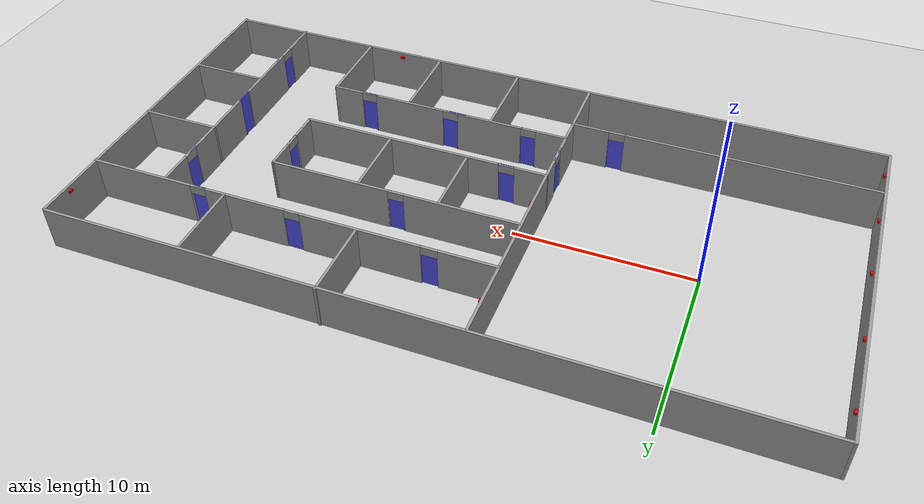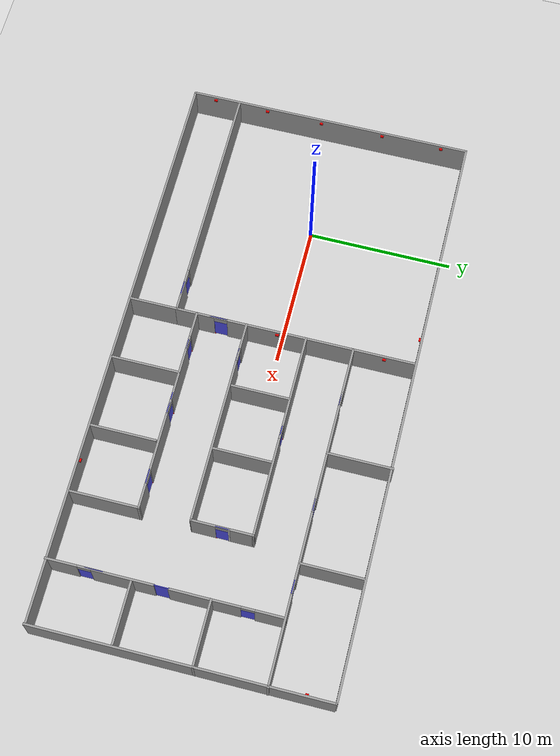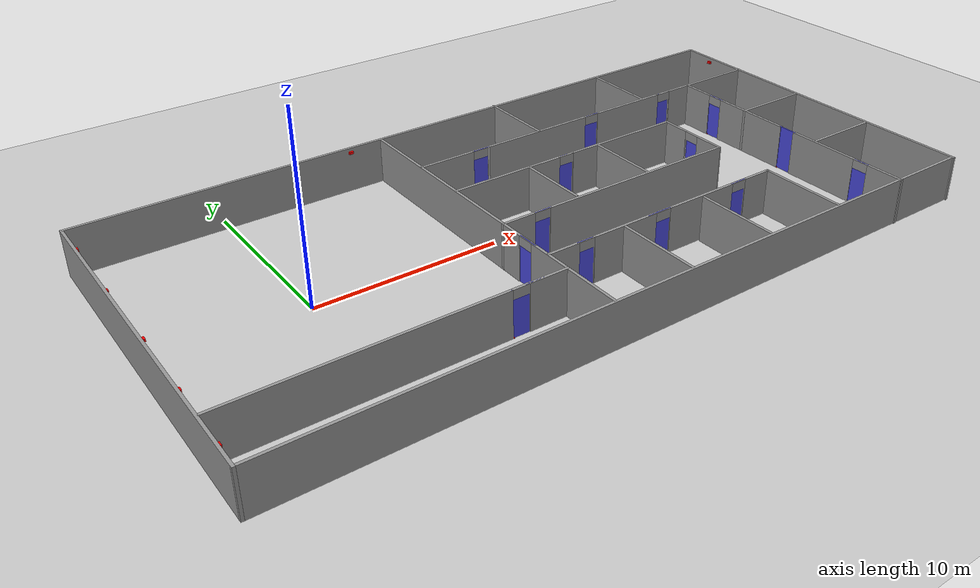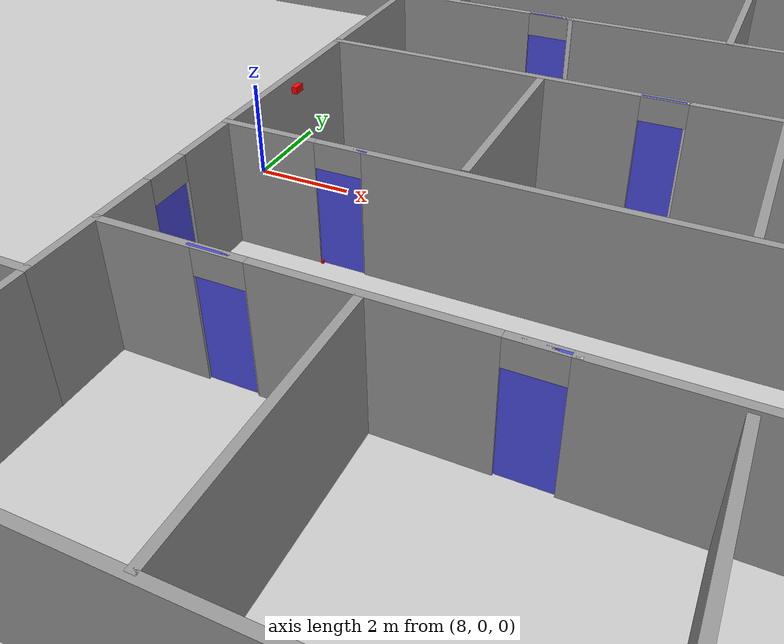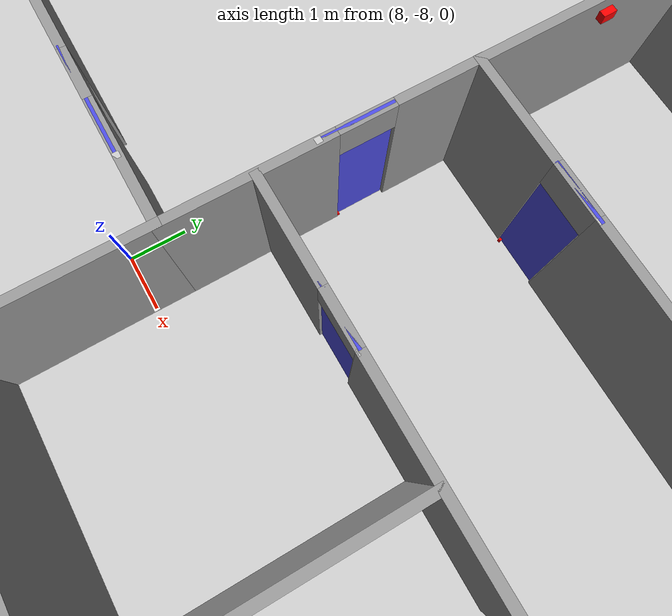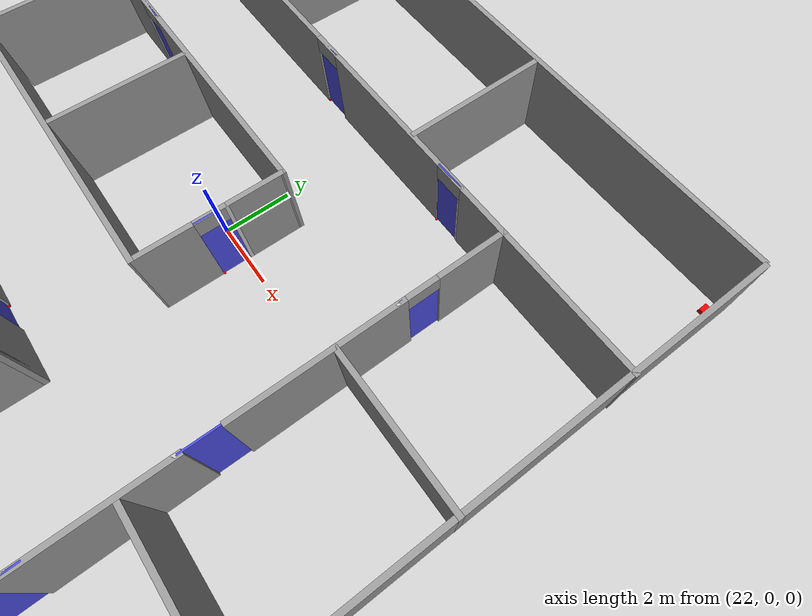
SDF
<sdf version="1.7">
 <world name="default">
  <light name="sun" type="directional">
   <pose>0 0 10 0 -0 0</pose>
   <diffuse>0.8 0.8 0.8 1</diffuse>
   <specular>0.2 0.2 0.2 1</specular>
   <attenuation>
    <range>1000</range>
    <constant>0.9</constant>
    <linear>0.01</linear>
    <quadratic>0.001</quadratic>
   </attenuation>
   <direction>-0.5 0.1 -0.9</direction>
   <spot><inner_angle>0</inner_angle><outer_angle>0</outer_angle><falloff>0</falloff></spot>
  </light>
  <model name="ground_plane">
   <static>1</static>
   <link name="link">
    <collision name="collision">
     <geometry><plane><normal>0 0 1</normal><size>100 100</size></plane></geometry>
     <surface><friction><ode><mu>100</mu><mu2>50</mu2></ode></friction></surface>
    </collision>
    <visual name="visual">
     <cast_shadows>0</cast_shadows>
     <geometry><plane><normal>0 0 1</normal><size>100 100</size></plane></geometry>
     <material>
      <script><uri>file://media/materials/scripts/gazebo.material</uri><name>Gazebo/Grey</name></script>
     </material>
    </visual>
   </link>
  </model>
  <gravity>0 0 -9.8</gravity>
  <magnetic_field>6e-06 2.3e-05 -4.2e-05</magnetic_field>
  <atmosphere type="adiabatic"/>
  <physics type="ode">
   <max_step_size>0.001</max_step_size>
   <real_time_factor>1</real_time_factor>
   <real_time_update_rate>1000</real_time_update_rate>
  </physics>
  <scene><ambient>0.4 0.4 0.4 1</ambient><background>0.7 0.7 0.7 1</background><shadows>1</shadows></scene>
  <spherical_coordinates>
   <surface_model>EARTH_WGS84</surface_model>
   <latitude_deg>0</latitude_deg>
   <longitude_deg>0</longitude_deg>
   <elevation>0</elevation>
   <heading_deg>0</heading_deg>
  </spherical_coordinates>
  <model name="new_surveillance_world">
   <pose>12.0889 -0.60412 0 0 -0 0</pose>
   <link name="Wall_0">
    <collision name="Wall_0_Collision">
     <geometry><box><size>40 0.15 2.5</size></box></geometry>
     <pose>0 0 1.25 0 -0 0</pose>
    </collision>
    <visual name="Wall_0_Visual">
     <pose>0 0 1.25 0 -0 0</pose>
     <geometry><box><size>40 0.15 2.5</size></box></geometry>
     <material>
      <script><uri>file://media/materials/scripts/gazebo.material</uri><name>Gazebo/Grey</name></script>
      <ambient>1 1 1 1</ambient>
     </material>
     <meta><layer>0</layer></meta>
    </visual>
    <pose>-0.094918 -9.92648 0 0 -0 0</pose>
   </link>
   <link name="Wall_25">
    <collision name="Wall_25_Collision">
     <geometry><box><size>20 0.15 2.5</size></box></geometry>
     <pose>0 0 1.25 0 -0 0</pose>
    </collision>
    <visual name="Wall_25_Visual">
     <pose>0 0 1.25 0 -0 0</pose>
     <geometry><box><size>20 0.15 2.5</size></box></geometry>
     <material>
      <script><uri>file://media/materials/scripts/gazebo.material</uri><name>Gazebo/Grey</name></script>
      <ambient>1 1 1 1</ambient>
     </material>
     <meta><layer>0</layer></meta>
    </visual>
    <pose>19.9894 -0.065064 0 0 -0 1.5708</pose>
   </link>
   <link name="Wall_27">
    <pose>-11.5401 -6.63194 0 0 -0 0</pose>
    <visual name="Wall_27_Visual_0">
     <pose>-1.53194 0 1.25 0 -0 0</pose>
     <geometry><box><size>13.9361 0.15 2.5</size></box></geometry>
     <material>
      <script><uri>file://media/materials/scripts/gazebo.material</uri><name>Gazebo/Grey</name></script>
      <ambient>1 1 1 1</ambient>
     </material>
     <meta><layer>0</layer></meta>
    </visual>
    <collision name="Wall_27_Collision_0">
     <geometry><box><size>13.9361 0.15 2.5</size></box></geometry>
     <pose>-1.53194 0 1.25 0 -0 0</pose>
    </collision>
    <visual name="Wall_27_Visual_1">
     <pose>7.41806 0 1.25 0 -0 0</pose>
     <geometry><box><size>2.16387 0.15 2.5</size></box></geometry>
     <material>
      <script><uri>file://media/materials/scripts/gazebo.material</uri><name>Gazebo/Grey</name></script>
      <ambient>1 1 1 1</ambient>
     </material>
     <meta><layer>0</layer></meta>
    </visual>
    <collision name="Wall_27_Collision_1">
     <geometry><box><size>2.16387 0.15 2.5</size></box></geometry>
     <pose>7.41806 0 1.25 0 -0 0</pose>
    </collision>
    <visual name="Wall_27_Visual_2">
     <pose>5.88613 0 2.25 0 -0 0</pose>
     <geometry><box><size>0.9 0.15 0.5</size></box></geometry>
     <material>
      <script><uri>file://media/materials/scripts/gazebo.material</uri><name>Gazebo/Grey</name></script>
      <ambient>1 1 1 1</ambient>
     </material>
     <meta><layer>0</layer></meta>
    </visual>
    <collision name="Wall_27_Collision_2">
     <geometry><box><size>0.9 0.15 0.5</size></box></geometry>
     <pose>5.88613 0 2.25 0 -0 0</pose>
    </collision>
   </link>
   <link name="Wall_28">
    <pose>-3.1151 1.61459 0 0 -0 1.5708</pose>
    <visual name="Wall_28_Visual_0">
     <pose>-6.96456 0 1.25 0 -0 0</pose>
     <geometry><box><size>2.71394 0.15 2.5</size></box></geometry>
     <material>
      <script><uri>file://media/materials/scripts/gazebo.material</uri><name>Gazebo/Grey</name></script>
      <ambient>1 1 1 1</ambient>
     </material>
     <meta><layer>0</layer></meta>
    </visual>
    <collision name="Wall_28_Collision_0">
     <geometry><box><size>2.71394 0.15 2.5</size></box></geometry>
     <pose>-6.96456 0 1.25 0 -0 0</pose>
    </collision>
    <visual name="Wall_28_Visual_1">
     <pose>1.80697 0 1.25 0 -0 0</pose>
     <geometry><box><size>13.0291 0.15 2.5</size></box></geometry>
     <material>
      <script><uri>file://media/materials/scripts/gazebo.material</uri><name>Gazebo/Grey</name></script>
      <ambient>1 1 1 1</ambient>
     </material>
     <meta><layer>0</layer></meta>
    </visual>
    <collision name="Wall_28_Collision_1">
     <geometry><box><size>13.0291 0.15 2.5</size></box></geometry>
     <pose>1.80697 0 1.25 0 -0 0</pose>
    </collision>
    <visual name="Wall_28_Visual_2">
     <pose>-5.15759 0 2.25 0 -0 0</pose>
     <geometry><box><size>0.9 0.15 0.5</size></box></geometry>
     <material>
      <script><uri>file://media/materials/scripts/gazebo.material</uri><name>Gazebo/Grey</name></script>
      <ambient>1 1 1 1</ambient>
     </material>
     <meta><layer>0</layer></meta>
    </visual>
    <collision name="Wall_28_Collision_2">
     <geometry><box><size>0.9 0.15 0.5</size></box></geometry>
     <pose>-5.15759 0 2.25 0 -0 0</pose>
    </collision>
   </link>
   <link name="Wall_30">
    <collision name="Wall_30_Collision">
     <geometry><box><size>3.35736 0.15 2.5</size></box></geometry>
     <pose>0 0 1.25 0 -0 0</pose>
    </collision>
    <visual name="Wall_30_Visual">
     <pose>0 0 1.25 0 -0 0</pose>
     <geometry><box><size>3.35736 0.15 2.5</size></box></geometry>
     <material>
      <script><uri>file://media/materials/scripts/gazebo.material</uri><name>Gazebo/Grey</name></script>
      <ambient>1 1 1 1</ambient>
     </material>
     <meta><layer>0</layer></meta>
    </visual>
    <pose>-3.1151 -8.23541 0 0 -0 -1.5708</pose>
   </link>
   <link name="Wall_32">
    <pose>8.46992 5.62416 0 0 -0 0</pose>
    <visual name="Wall_32_Visual_0">
     <pose>-10.0174 0 1.25 0 -0 0</pose>
     <geometry><box><size>3.21511 0.15 2.5</size></box></geometry>
     <material>
      <script><uri>file://media/materials/scripts/gazebo.material</uri><name>Gazebo/Grey</name></script>
      <ambient>1 1 1 1</ambient>
     </material>
     <meta><layer>0</layer></meta>
    </visual>
    <collision name="Wall_32_Collision_0">
     <geometry><box><size>3.21511 0.15 2.5</size></box></geometry>
     <pose>-10.0174 0 1.25 0 -0 0</pose>
    </collision>
    <visual name="Wall_32_Visual_1">
     <pose>-4.16489 0 1.25 0 -0 0</pose>
     <geometry><box><size>6.69 0.15 2.5</size></box></geometry>
     <material>
      <script><uri>file://media/materials/scripts/gazebo.material</uri><name>Gazebo/Grey</name></script>
      <ambient>1 1 1 1</ambient>
     </material>
     <meta><layer>0</layer></meta>
    </visual>
    <collision name="Wall_32_Collision_1">
     <geometry><box><size>6.69 0.15 2.5</size></box></geometry>
     <pose>-4.16489 0 1.25 0 -0 0</pose>
    </collision>
    <visual name="Wall_32_Visual_2">
     <pose>2.39011 0 1.25 0 -0 0</pose>
     <geometry><box><size>4.62 0.15 2.5</size></box></geometry>
     <material>
      <script><uri>file://media/materials/scripts/gazebo.material</uri><name>Gazebo/Grey</name></script>
      <ambient>1 1 1 1</ambient>
     </material>
     <meta><layer>0</layer></meta>
    </visual>
    <collision name="Wall_32_Collision_2">
     <geometry><box><size>4.62 0.15 2.5</size></box></geometry>
     <pose>2.39011 0 1.25 0 -0 0</pose>
    </collision>
    <visual name="Wall_32_Visual_3">
     <pose>8.61256 0 1.25 0 -0 0</pose>
     <geometry><box><size>6.02489 0.15 2.5</size></box></geometry>
     <material>
      <script><uri>file://media/materials/scripts/gazebo.material</uri><name>Gazebo/Grey</name></script>
      <ambient>1 1 1 1</ambient>
     </material>
     <meta><layer>0</layer></meta>
    </visual>
    <collision name="Wall_32_Collision_3">
     <geometry><box><size>6.02489 0.15 2.5</size></box></geometry>
     <pose>8.61256 0 1.25 0 -0 0</pose>
    </collision>
    <visual name="Wall_32_Visual_4">
     <pose>-7.95989 0 2.25 0 -0 0</pose>
     <geometry><box><size>0.9 0.15 0.5</size></box></geometry>
     <material>
      <script><uri>file://media/materials/scripts/gazebo.material</uri><name>Gazebo/Grey</name></script>
      <ambient>1 1 1 1</ambient>
     </material>
     <meta><layer>0</layer></meta>
    </visual>
    <collision name="Wall_32_Collision_4">
     <geometry><box><size>0.9 0.15 0.5</size></box></geometry>
     <pose>-7.95989 0 2.25 0 -0 0</pose>
    </collision>
    <visual name="Wall_32_Visual_5">
     <pose>-0.369888 0 2.25 0 -0 0</pose>
     <geometry><box><size>0.9 0.15 0.5</size></box></geometry>
     <material>
      <script><uri>file://media/materials/scripts/gazebo.material</uri><name>Gazebo/Grey</name></script>
      <ambient>1 1 1 1</ambient>
     </material>
     <meta><layer>0</layer></meta>
    </visual>
    <collision name="Wall_32_Collision_5">
     <geometry><box><size>0.9 0.15 0.5</size></box></geometry>
     <pose>-0.369888 0 2.25 0 -0 0</pose>
    </collision>
    <visual name="Wall_32_Visual_6">
     <pose>5.15011 0 2.25 0 -0 0</pose>
     <geometry><box><size>0.9 0.15 0.5</size></box></geometry>
     <material>
      <script><uri>file://media/materials/scripts/gazebo.material</uri><name>Gazebo/Grey</name></script>
      <ambient>1 1 1 1</ambient>
     </material>
     <meta><layer>0</layer></meta>
    </visual>
    <collision name="Wall_32_Collision_6">
     <geometry><box><size>0.9 0.15 0.5</size></box></geometry>
     <pose>5.15011 0 2.25 0 -0 0</pose>
    </collision>
   </link>
   <link name="Wall_34">
    <pose>15.646 -2.17584 0 0 -0 -1.5708</pose>
    <visual name="Wall_34_Visual_0">
     <pose>-6.85992 0 1.25 0 -0 0</pose>
     <geometry><box><size>2.03016 0.15 2.5</size></box></geometry>
     <material>
      <script><uri>file://media/materials/scripts/gazebo.material</uri><name>Gazebo/Grey</name></script>
      <ambient>1 1 1 1</ambient>
     </material>
     <meta><layer>0</layer></meta>
    </visual>
    <collision name="Wall_34_Collision_0">
     <geometry><box><size>2.03016 0.15 2.5</size></box></geometry>
     <pose>-6.85992 0 1.25 0 -0 0</pose>
    </collision>
    <visual name="Wall_34_Visual_1">
     <pose>-2.58884 0 1.25 0 -0 0</pose>
     <geometry><box><size>4.712 0.15 2.5</size></box></geometry>
     <material>
      <script><uri>file://media/materials/scripts/gazebo.material</uri><name>Gazebo/Grey</name></script>
      <ambient>1 1 1 1</ambient>
     </material>
     <meta><layer>0</layer></meta>
    </visual>
    <collision name="Wall_34_Collision_1">
     <geometry><box><size>4.712 0.15 2.5</size></box></geometry>
     <pose>-2.58884 0 1.25 0 -0 0</pose>
    </collision>
    <visual name="Wall_34_Visual_2">
     <pose>2.74716 0 1.25 0 -0 0</pose>
     <geometry><box><size>4.16 0.15 2.5</size></box></geometry>
     <material>
      <script><uri>file://media/materials/scripts/gazebo.material</uri><name>Gazebo/Grey</name></script>
      <ambient>1 1 1 1</ambient>
     </material>
     <meta><layer>0</layer></meta>
    </visual>
    <collision name="Wall_34_Collision_2">
     <geometry><box><size>4.16 0.15 2.5</size></box></geometry>
     <pose>2.74716 0 1.25 0 -0 0</pose>
    </collision>
    <visual name="Wall_34_Visual_3">
     <pose>6.80108 0 1.25 0 -0 0</pose>
     <geometry><box><size>2.14784 0.15 2.5</size></box></geometry>
     <material>
      <script><uri>file://media/materials/scripts/gazebo.material</uri><name>Gazebo/Grey</name></script>
      <ambient>1 1 1 1</ambient>
     </material>
     <meta><layer>0</layer></meta>
    </visual>
    <collision name="Wall_34_Collision_3">
     <geometry><box><size>2.14784 0.15 2.5</size></box></geometry>
     <pose>6.80108 0 1.25 0 -0 0</pose>
    </collision>
    <visual name="Wall_34_Visual_4">
     <pose>-5.39484 0 2.25 0 -0 0</pose>
     <geometry><box><size>0.9 0.15 0.5</size></box></geometry>
     <material>
      <script><uri>file://media/materials/scripts/gazebo.material</uri><name>Gazebo/Grey</name></script>
      <ambient>1 1 1 1</ambient>
     </material>
     <meta><layer>0</layer></meta>
    </visual>
    <collision name="Wall_34_Collision_4">
     <geometry><box><size>0.9 0.15 0.5</size></box></geometry>
     <pose>-5.39484 0 2.25 0 -0 0</pose>
    </collision>
    <visual name="Wall_34_Visual_5">
     <pose>-0.23284 0 2.25 0 -0 0</pose>
     <geometry><box><size>0 0.15 0.5</size></box></geometry>
     <material>
      <script><uri>file://media/materials/scripts/gazebo.material</uri><name>Gazebo/Grey</name></script>
      <ambient>1 1 1 1</ambient>
     </material>
     <meta><layer>0</layer></meta>
    </visual>
    <collision name="Wall_34_Collision_5">
     <geometry><box><size>0 0.15 0.5</size></box></geometry>
     <pose>-0.23284 0 2.25 0 -0 0</pose>
    </collision>
    <visual name="Wall_34_Visual_6">
     <pose>5.27716 0 2.25 0 -0 0</pose>
     <geometry><box><size>0.9 0.15 0.5</size></box></geometry>
     <material>
      <script><uri>file://media/materials/scripts/gazebo.material</uri><name>Gazebo/Grey</name></script>
      <ambient>1 1 1 1</ambient>
     </material>
     <meta><layer>0</layer></meta>
    </visual>
    <collision name="Wall_34_Collision_6">
     <geometry><box><size>0.9 0.15 0.5</size></box></geometry>
     <pose>5.27716 0 2.25 0 -0 0</pose>
    </collision>
   </link>
   <link name="Wall_36">
    <pose>3.93738 2.36994 0 0 -0 0</pose>
    <visual name="Wall_36_Visual_0">
     <pose>-3.86818 0 1.25 0 -0 0</pose>
     <geometry><box><size>6.51365 0.15 2.5</size></box></geometry>
     <material>
      <script><uri>file://media/materials/scripts/gazebo.material</uri><name>Gazebo/Grey</name></script>
      <ambient>1 1 1 1</ambient>
     </material>
     <meta><layer>0</layer></meta>
    </visual>
    <collision name="Wall_36_Collision_0">
     <geometry><box><size>6.51365 0.15 2.5</size></box></geometry>
     <pose>-3.86818 0 1.25 0 -0 0</pose>
    </collision>
    <visual name="Wall_36_Visual_1">
     <pose>3.70682 0 1.25 0 -0 0</pose>
     <geometry><box><size>6.83635 0.15 2.5</size></box></geometry>
     <material>
      <script><uri>file://media/materials/scripts/gazebo.material</uri><name>Gazebo/Grey</name></script>
      <ambient>1 1 1 1</ambient>
     </material>
     <meta><layer>0</layer></meta>
    </visual>
    <collision name="Wall_36_Collision_1">
     <geometry><box><size>6.83635 0.15 2.5</size></box></geometry>
     <pose>3.70682 0 1.25 0 -0 0</pose>
    </collision>
    <visual name="Wall_36_Visual_2">
     <pose>-0.161353 0 2.25 0 -0 0</pose>
     <geometry><box><size>0.9 0.15 0.5</size></box></geometry>
     <material>
      <script><uri>file://media/materials/scripts/gazebo.material</uri><name>Gazebo/Grey</name></script>
      <ambient>1 1 1 1</ambient>
     </material>
     <meta><layer>0</layer></meta>
    </visual>
    <collision name="Wall_36_Collision_2">
     <geometry><box><size>0.9 0.15 0.5</size></box></geometry>
     <pose>-0.161353 0 2.25 0 -0 0</pose>
    </collision>
   </link>
   <link name="Wall_38">
    <pose>3.93032 -1.7507 0 0 -0 3.14159</pose>
    <visual name="Wall_38_Visual_0">
     <pose>-1.38735 0 1.25 0 -0 0</pose>
     <geometry><box><size>11.4753 0.15 2.5</size></box></geometry>
     <material>
      <script><uri>file://media/materials/scripts/gazebo.material</uri><name>Gazebo/Grey</name></script>
      <ambient>1 1 1 1</ambient>
     </material>
     <meta><layer>0</layer></meta>
    </visual>
    <collision name="Wall_38_Collision_0">
     <geometry><box><size>11.4753 0.15 2.5</size></box></geometry>
     <pose>-1.38735 0 1.25 0 -0 0</pose>
    </collision>
    <visual name="Wall_38_Visual_1">
     <pose>6.18765 0 1.25 0 -0 0</pose>
     <geometry><box><size>1.87471 0.15 2.5</size></box></geometry>
     <material>
      <script><uri>file://media/materials/scripts/gazebo.material</uri><name>Gazebo/Grey</name></script>
      <ambient>1 1 1 1</ambient>
     </material>
     <meta><layer>0</layer></meta>
    </visual>
    <collision name="Wall_38_Collision_1">
     <geometry><box><size>1.87471 0.15 2.5</size></box></geometry>
     <pose>6.18765 0 1.25 0 -0 0</pose>
    </collision>
    <visual name="Wall_38_Visual_2">
     <pose>4.80029 0 2.25 0 -0 0</pose>
     <geometry><box><size>0.9 0.15 0.5</size></box></geometry>
     <material>
      <script><uri>file://media/materials/scripts/gazebo.material</uri><name>Gazebo/Grey</name></script>
      <ambient>1 1 1 1</ambient>
     </material>
     <meta><layer>0</layer></meta>
    </visual>
    <collision name="Wall_38_Collision_2">
     <geometry><box><size>0.9 0.15 0.5</size></box></geometry>
     <pose>4.80029 0 2.25 0 -0 0</pose>
    </collision>
   </link>
   <link name="Wall_4">
    <collision name="Wall_4_Collision">
     <geometry><box><size>40 0.15 2.5</size></box></geometry>
     <pose>0 0 1.25 0 -0 0</pose>
    </collision>
    <visual name="Wall_4_Visual">
     <pose>0 0 1.25 0 -0 0</pose>
     <geometry><box><size>40 0.15 2.5</size></box></geometry>
     <material>
      <script><uri>file://media/materials/scripts/gazebo.material</uri><name>Gazebo/Grey</name></script>
      <ambient>1 1 1 1</ambient>
     </material>
     <meta><layer>0</layer></meta>
    </visual>
    <pose>-0.005001 9.92216 0 0 -0 3.14159</pose>
   </link>
   <link name="Wall_41">
    <pose>3.96992 -5.21171 0 0 -0 0</pose>
    <visual name="Wall_41_Visual_0">
     <pose>-6.23044 0 1.25 0 -0 0</pose>
     <geometry><box><size>1.78911 0.15 2.5</size></box></geometry>
     <material>
      <script><uri>file://media/materials/scripts/gazebo.material</uri><name>Gazebo/Grey</name></script>
      <ambient>1 1 1 1</ambient>
     </material>
     <meta><layer>0</layer></meta>
    </visual>
    <collision name="Wall_41_Collision_0">
     <geometry><box><size>1.78911 0.15 2.5</size></box></geometry>
     <pose>-6.23044 0 1.25 0 -0 0</pose>
    </collision>
    <visual name="Wall_41_Visual_1">
     <pose>-2.53989 0 1.25 0 -0 0</pose>
     <geometry><box><size>3.792 0.15 2.5</size></box></geometry>
     <material>
      <script><uri>file://media/materials/scripts/gazebo.material</uri><name>Gazebo/Grey</name></script>
      <ambient>1 1 1 1</ambient>
     </material>
     <meta><layer>0</layer></meta>
    </visual>
    <collision name="Wall_41_Collision_1">
     <geometry><box><size>3.792 0.15 2.5</size></box></geometry>
     <pose>-2.53989 0 1.25 0 -0 0</pose>
    </collision>
    <visual name="Wall_41_Visual_2">
     <pose>2.35911 0 1.25 0 -0 0</pose>
     <geometry><box><size>4.206 0.15 2.5</size></box></geometry>
     <material>
      <script><uri>file://media/materials/scripts/gazebo.material</uri><name>Gazebo/Grey</name></script>
      <ambient>1 1 1 1</ambient>
     </material>
     <meta><layer>0</layer></meta>
    </visual>
    <collision name="Wall_41_Collision_2">
     <geometry><box><size>4.206 0.15 2.5</size></box></geometry>
     <pose>2.35911 0 1.25 0 -0 0</pose>
    </collision>
    <visual name="Wall_41_Visual_3">
     <pose>6.24356 0 1.25 0 -0 0</pose>
     <geometry><box><size>1.76289 0.15 2.5</size></box></geometry>
     <material>
      <script><uri>file://media/materials/scripts/gazebo.material</uri><name>Gazebo/Grey</name></script>
      <ambient>1 1 1 1</ambient>
     </material>
     <meta><layer>0</layer></meta>
    </visual>
    <collision name="Wall_41_Collision_3">
     <geometry><box><size>1.76289 0.15 2.5</size></box></geometry>
     <pose>6.24356 0 1.25 0 -0 0</pose>
    </collision>
    <visual name="Wall_41_Visual_4">
     <pose>-4.88589 0 2.25 0 -0 0</pose>
     <geometry><box><size>0.9 0.15 0.5</size></box></geometry>
     <material>
      <script><uri>file://media/materials/scripts/gazebo.material</uri><name>Gazebo/Grey</name></script>
      <ambient>1 1 1 1</ambient>
     </material>
     <meta><layer>0</layer></meta>
    </visual>
    <collision name="Wall_41_Collision_4">
     <geometry><box><size>0.9 0.15 0.5</size></box></geometry>
     <pose>-4.88589 0 2.25 0 -0 0</pose>
    </collision>
    <visual name="Wall_41_Visual_5">
     <pose>-0.193888 0 2.25 0 -0 0</pose>
     <geometry><box><size>0.9 0.15 0.5</size></box></geometry>
     <material>
      <script><uri>file://media/materials/scripts/gazebo.material</uri><name>Gazebo/Grey</name></script>
      <ambient>1 1 1 1</ambient>
     </material>
     <meta><layer>0</layer></meta>
    </visual>
    <collision name="Wall_41_Collision_5">
     <geometry><box><size>0.9 0.15 0.5</size></box></geometry>
     <pose>-0.193888 0 2.25 0 -0 0</pose>
    </collision>
    <visual name="Wall_41_Visual_6">
     <pose>4.91211 0 2.25 0 -0 0</pose>
     <geometry><box><size>0.9 0.15 0.5</size></box></geometry>
     <material>
      <script><uri>file://media/materials/scripts/gazebo.material</uri><name>Gazebo/Grey</name></script>
      <ambient>1 1 1 1</ambient>
     </material>
     <meta><layer>0</layer></meta>
    </visual>
    <collision name="Wall_41_Collision_6">
     <geometry><box><size>0.9 0.15 0.5</size></box></geometry>
     <pose>4.91211 0 2.25 0 -0 0</pose>
    </collision>
   </link>
   <link name="Wall_42">
    <collision name="Wall_42_Collision">
     <geometry><box><size>4.75 0.15 2.5</size></box></geometry>
     <pose>0 0 1.25 0 -0 0</pose>
    </collision>
    <visual name="Wall_42_Visual">
     <pose>0 0 1.25 0 -0 0</pose>
     <geometry><box><size>4.75 0.15 2.5</size></box></geometry>
     <material>
      <script><uri>file://media/materials/scripts/gazebo.material</uri><name>Gazebo/Grey</name></script>
      <ambient>1 1 1 1</ambient>
     </material>
     <meta><layer>0</layer></meta>
    </visual>
    <pose>11.0199 -7.51171 0 0 -0 -1.5708</pose>
   </link>
   <link name="Wall_44">
    <collision name="Wall_44_Collision">
     <geometry><box><size>4.5 0.15 2.5</size></box></geometry>
     <pose>0 0 1.25 0 -0 0</pose>
    </collision>
    <visual name="Wall_44_Visual">
     <pose>0 0 1.25 0 -0 0</pose>
     <geometry><box><size>4.5 0.15 2.5</size></box></geometry>
     <material>
      <script><uri>file://media/materials/scripts/gazebo.material</uri><name>Gazebo/Grey</name></script>
      <ambient>1 1 1 1</ambient>
     </material>
     <meta><layer>0</layer></meta>
    </visual>
    <pose>4.4419 7.81506 0 0 -0 -1.5708</pose>
   </link>
   <link name="Wall_46">
    <collision name="Wall_46_Collision">
     <geometry><box><size>4.25 0.15 2.5</size></box></geometry>
     <pose>0 0 1.25 0 -0 0</pose>
    </collision>
    <visual name="Wall_46_Visual">
     <pose>0 0 1.25 0 -0 0</pose>
     <geometry><box><size>4.25 0.15 2.5</size></box></geometry>
     <material>
      <script><uri>file://media/materials/scripts/gazebo.material</uri><name>Gazebo/Grey</name></script>
      <ambient>1 1 1 1</ambient>
     </material>
     <meta><layer>0</layer></meta>
    </visual>
    <pose>12.0165 7.74267 0 0 -0 -1.5708</pose>
   </link>
   <link name="Wall_48">
    <pose>10.9839 0.309616 0 0 -0 -1.57251</pose>
    <visual name="Wall_48_Visual_0">
     <pose>-1.29852 0 1.25 0 -0 0</pose>
     <geometry><box><size>1.6736 0.15 2.5</size></box></geometry>
     <material>
      <script><uri>file://media/materials/scripts/gazebo.material</uri><name>Gazebo/Grey</name></script>
      <ambient>1 1 1 1</ambient>
     </material>
     <meta><layer>0</layer></meta>
    </visual>
    <collision name="Wall_48_Collision_0">
     <geometry><box><size>1.6736 0.15 2.5</size></box></geometry>
     <pose>-1.29852 0 1.25 0 -0 0</pose>
    </collision>
    <visual name="Wall_48_Visual_1">
     <pose>1.2868 0 1.25 0 -0 0</pose>
     <geometry><box><size>1.69704 0.15 2.5</size></box></geometry>
     <material>
      <script><uri>file://media/materials/scripts/gazebo.material</uri><name>Gazebo/Grey</name></script>
      <ambient>1 1 1 1</ambient>
     </material>
     <meta><layer>0</layer></meta>
    </visual>
    <collision name="Wall_48_Collision_1">
     <geometry><box><size>1.69704 0.15 2.5</size></box></geometry>
     <pose>1.2868 0 1.25 0 -0 0</pose>
    </collision>
    <visual name="Wall_48_Visual_2">
     <pose>-0.011721 0 2.25 0 -0 0</pose>
     <geometry><box><size>0.9 0.15 0.5</size></box></geometry>
     <material>
      <script><uri>file://media/materials/scripts/gazebo.material</uri><name>Gazebo/Grey</name></script>
      <ambient>1 1 1 1</ambient>
     </material>
     <meta><layer>0</layer></meta>
    </visual>
    <collision name="Wall_48_Collision_2">
     <geometry><box><size>0.9 0.15 0.5</size></box></geometry>
     <pose>-0.011721 0 2.25 0 -0 0</pose>
    </collision>
   </link>
   <link name="Wall_50">
    <collision name="Wall_50_Collision">
     <geometry><box><size>4.5 0.15 2.5</size></box></geometry>
     <pose>0 0 1.25 0 -0 0</pose>
    </collision>
    <visual name="Wall_50_Visual">
     <pose>0 0 1.25 0 -0 0</pose>
     <geometry><box><size>4.5 0.15 2.5</size></box></geometry>
     <material>
      <script><uri>file://media/materials/scripts/gazebo.material</uri><name>Gazebo/Grey</name></script>
      <ambient>1 1 1 1</ambient>
     </material>
     <meta><layer>0</layer></meta>
    </visual>
    <pose>17.8178 0.843208 0 0 -0 0</pose>
   </link>
   <link name="Wall_54">
    <collision name="Wall_54_Collision">
     <geometry><box><size>4.25 0.15 2.5</size></box></geometry>
     <pose>0 0 1.25 0 -0 0</pose>
    </collision>
    <visual name="Wall_54_Visual">
     <pose>0 0 1.25 0 -0 0</pose>
     <geometry><box><size>4.25 0.15 2.5</size></box></geometry>
     <material>
      <script><uri>file://media/materials/scripts/gazebo.material</uri><name>Gazebo/Grey</name></script>
      <ambient>1 1 1 1</ambient>
     </material>
     <meta><layer>0</layer></meta>
    </visual>
    <pose>17.786 -4.325 0 0 -0 0</pose>
   </link>
   <link name="Wall_56">
    <collision name="Wall_56_Collision">
     <geometry><box><size>4.75 0.15 2.5</size></box></geometry>
     <pose>0 0 1.25 0 -0 0</pose>
    </collision>
    <visual name="Wall_56_Visual">
     <pose>0 0 1.25 0 -0 0</pose>
     <geometry><box><size>4.75 0.15 2.5</size></box></geometry>
     <material>
      <script><uri>file://media/materials/scripts/gazebo.material</uri><name>Gazebo/Grey</name></script>
      <ambient>1 1 1 1</ambient>
     </material>
     <meta><layer>0</layer></meta>
    </visual>
    <pose>1.33803 -7.545 0 0 -0 -1.5708</pose>
   </link>
   <link name="Wall_58">
    <collision name="Wall_58_Collision">
     <geometry><box><size>4.5 0.15 2.5</size></box></geometry>
     <pose>0 0 1.25 0 -0 0</pose>
    </collision>
    <visual name="Wall_58_Visual">
     <pose>0 0 1.25 0 -0 0</pose>
     <geometry><box><size>4.5 0.15 2.5</size></box></geometry>
     <material>
      <script><uri>file://media/materials/scripts/gazebo.material</uri><name>Gazebo/Grey</name></script>
      <ambient>1 1 1 1</ambient>
     </material>
     <meta><layer>0</layer></meta>
    </visual>
    <pose>6.35203 -7.604 0 0 -0 -1.5708</pose>
   </link>
   <link name="Wall_6">
    <collision name="Wall_6_Collision">
     <geometry><box><size>20 0.15 2.5</size></box></geometry>
     <pose>0 0 1.25 0 -0 0</pose>
    </collision>
    <visual name="Wall_6_Visual">
     <pose>0 0 1.25 0 -0 0</pose>
     <geometry><box><size>20 0.15 2.5</size></box></geometry>
     <material>
      <script><uri>file://media/materials/scripts/gazebo.material</uri><name>Gazebo/Grey</name></script>
      <ambient>1 1 1 1</ambient>
     </material>
     <meta><layer>0</layer></meta>
    </visual>
    <pose>-20.0199 -0.001483 0 0 -0 1.5708</pose>
   </link>
   <link name="Wall_60">
    <collision name="Wall_60_Collision">
     <geometry><box><size>4 0.15 2.5</size></box></geometry>
     <pose>0 0 1.25 0 -0 0</pose>
    </collision>
    <visual name="Wall_60_Visual">
     <pose>0 0 1.25 0 -0 0</pose>
     <geometry><box><size>4 0.15 2.5</size></box></geometry>
     <material>
      <script><uri>file://media/materials/scripts/gazebo.material</uri><name>Gazebo/Grey</name></script>
      <ambient>1 1 1 1</ambient>
     </material>
     <meta><layer>0</layer></meta>
    </visual>
    <pose>1.38403 0.359998 0 0 -0 1.5708</pose>
   </link>
   <link name="Wall_62">
    <collision name="Wall_62_Collision">
     <geometry><box><size>4 0.15 2.5</size></box></geometry>
     <pose>0 0 1.25 0 -0 0</pose>
    </collision>
    <visual name="Wall_62_Visual">
     <pose>0 0 1.25 0 -0 0</pose>
     <geometry><box><size>4 0.15 2.5</size></box></geometry>
     <material>
      <script><uri>file://media/materials/scripts/gazebo.material</uri><name>Gazebo/Grey</name></script>
      <ambient>1 1 1 1</ambient>
     </material>
     <meta><layer>0</layer></meta>
    </visual>
    <pose>5.93803 0.327998 0 0 -0 -1.5708</pose>
   </link>
   <static>1</static>
  </model>
  <model name="door_1">
   <link name="door_frame">
    <pose>0.705849 0 1.25 0 -0 0</pose>
    <kinematic>1</kinematic>
    <inertial>
     <inertia><ixx>1</ixx><ixy>0</ixy><ixz>0</ixz><iyy>1</iyy><iyz>0</iyz><izz>1</izz></inertia>
     <mass>1</mass>
    </inertial>
    <visual name="frame_visual">
     <geometry><box><size>0.1 0.1 2.5</size></box></geometry>
     <material>
      <ambient>0.7 0.7 0.7 1</ambient>
      <diffuse>0.8 0.8 0.8 1</diffuse>
      <shader type="pixel"><normal_map>__default__</normal_map></shader>
      <script><name>ModelPreview_2::door_frame::frame_visual_MATERIAL_</name><uri>__default__</uri></script>
      <specular>0 0 0 1</specular>
      <emissive>0 0 0 1</emissive>
     </material>
    </visual>
    <collision name="frame_collision">
     <geometry><box><size>0.1 0.1 2.5</size></box></geometry>
     <surface>
      <friction>
       <ode><mu>1</mu><mu2>1</mu2><fdir1>0 0 0</fdir1><slip1>0</slip1><slip2>0</slip2></ode>
       <torsional>
        <coefficient>1</coefficient>
        <patch_radius>0</patch_radius>
        <surface_radius>0</surface_radius>
        <use_patch_radius>1</use_patch_radius>
        <ode><slip>0</slip></ode>
       </torsional>
      </friction>
      <bounce><restitution_coefficient>0</restitution_coefficient><threshold>1e+06</threshold></bounce>
      <contact>
       <collide_without_contact>0</collide_without_contact>
       <collide_without_contact_bitmask>1</collide_without_contact_bitmask>
       <collide_bitmask>1</collide_bitmask>
       <ode>
        <soft_cfm>0</soft_cfm>
        <soft_erp>0.2</soft_erp>
        <kp>1e+13</kp>
        <kd>1</kd>
        <max_vel>0.01</max_vel>
        <min_depth>0</min_depth>
       </ode>
       <bullet>
        <split_impulse>1</split_impulse>
        <split_impulse_penetration_threshold>-0.01</split_impulse_penetration_threshold>
        <soft_cfm>0</soft_cfm>
        <soft_erp>0.2</soft_erp>
        <kp>1e+13</kp>
        <kd>1</kd>
       </bullet>
      </contact>
     </surface>
    </collision>
   </link>
   <link name="door">
    <kinematic>1</kinematic>
    <pose>-0.288809 0 1.25 0 -0 0</pose>
    <inertial>
     <inertia><ixx>1.96777</ixx><ixy>0</ixy><ixz>0</ixz><iyy>3.08912</iyy><iyz>0</iyz><izz>1.12292</izz></inertia>
     <mass>3.77661</mass>
    </inertial>
    <visual name="door_visual">
     <geometry><box><size>1.88826 0.05 2.5</size></box></geometry>
     <material>
      <ambient>0.2 0.2 0.8 1</ambient>
      <diffuse>0.3 0.3 0.9 1</diffuse>
      <shader type="pixel"/>
      <script><name>ModelPreview_2::door::door_visual_MATERIAL_</name><uri>__default__</uri></script>
     </material>
    </visual>
    <collision name="door_collision">
     <geometry><box><size>1.88826 0.05 2.5</size></box></geometry>
     <surface>
      <friction>
       <ode><mu>1</mu><mu2>1</mu2><fdir1>0 0 0</fdir1><slip1>0</slip1><slip2>0</slip2></ode>
       <torsional>
        <coefficient>1</coefficient>
        <patch_radius>0</patch_radius>
        <surface_radius>0</surface_radius>
        <use_patch_radius>1</use_patch_radius>
        <ode><slip>0</slip></ode>
       </torsional>
      </friction>
      <bounce><restitution_coefficient>0</restitution_coefficient><threshold>1e+06</threshold></bounce>
      <contact>
       <collide_without_contact>0</collide_without_contact>
       <collide_without_contact_bitmask>1</collide_without_contact_bitmask>
       <collide_bitmask>1</collide_bitmask>
       <ode>
        <soft_cfm>0</soft_cfm>
        <soft_erp>0.2</soft_erp>
        <kp>1e+13</kp>
        <kd>1</kd>
        <max_vel>0.01</max_vel>
        <min_depth>0</min_depth>
       </ode>
       <bullet>
        <split_impulse>1</split_impulse>
        <split_impulse_penetration_threshold>-0.01</split_impulse_penetration_threshold>
        <soft_cfm>0</soft_cfm>
        <soft_erp>0.2</soft_erp>
        <kp>1e+13</kp>
        <kd>1</kd>
       </bullet>
      </contact>
     </surface>
    </collision>
   </link>
   <joint name="door_joint" type="prismatic">
    <parent>door_frame</parent>
    <child>door</child>
    <axis>
     <xyz>1 0 0</xyz>
     <limit><lower>0</lower><upper>2</upper><effort>-1</effort><velocity>-1</velocity></limit>
     <dynamics>
      <spring_reference>0</spring_reference>
      <spring_stiffness>0</spring_stiffness>
      <damping>0</damping>
      <friction>0</friction>
     </dynamics>
    </axis>
    <physics>
     <ode><limit><cfm>0</cfm><erp>0.2</erp></limit><suspension><cfm>0</cfm><erp>0.2</erp></suspension></ode>
    </physics>
   </joint>
   <static>0</static>
   <plugin name="door_control_plugin" filename="libdoor_control_plugin.so">
    <door_joint>door_joint</door_joint>
    <speed>1.0</speed>
    <open_target>1.0</open_target>
    <close_target>0.0</close_target>
   </plugin>
   <pose>7.159 -7.25541 0 0 -0 0</pose>
  </model>
  <model name="door_2">
   <link name="door_frame">
    <pose>0.25 -0 1.25 0 -0 0</pose>
    <kinematic>1</kinematic>
    <inertial>
     <inertia><ixx>1</ixx><ixy>0</ixy><ixz>0</ixz><iyy>1</iyy><iyz>0</iyz><izz>1</izz></inertia>
     <mass>1</mass>
    </inertial>
    <visual name="frame_visual">
     <geometry><box><size>0.1 0.1 2.5</size></box></geometry>
     <material>
      <ambient>0.7 0.7 0.7 1</ambient>
      <diffuse>0.8 0.8 0.8 1</diffuse>
      <shader type="pixel"><normal_map>__default__</normal_map></shader>
      <script><name>ModelPreview_2::door_frame::frame_visual_MATERIAL_</name><uri>__default__</uri></script>
      <specular>0 0 0 1</specular>
      <emissive>0 0 0 1</emissive>
     </material>
    </visual>
    <collision name="frame_collision">
     <geometry><box><size>0.1 0.1 2.5</size></box></geometry>
     <surface>
      <friction>
       <ode><mu>1</mu><mu2>1</mu2><fdir1>0 0 0</fdir1><slip1>0</slip1><slip2>0</slip2></ode>
       <torsional>
        <coefficient>1</coefficient>
        <patch_radius>0</patch_radius>
        <surface_radius>0</surface_radius>
        <use_patch_radius>1</use_patch_radius>
        <ode><slip>0</slip></ode>
       </torsional>
      </friction>
      <bounce><restitution_coefficient>0</restitution_coefficient><threshold>1e+06</threshold></bounce>
      <contact>
       <collide_without_contact>0</collide_without_contact>
       <collide_without_contact_bitmask>1</collide_without_contact_bitmask>
       <collide_bitmask>1</collide_bitmask>
       <ode>
        <soft_cfm>0</soft_cfm>
        <soft_erp>0.2</soft_erp>
        <kp>1e+13</kp>
        <kd>1</kd>
        <max_vel>0.01</max_vel>
        <min_depth>0</min_depth>
       </ode>
       <bullet>
        <split_impulse>1</split_impulse>
        <split_impulse_penetration_threshold>-0.01</split_impulse_penetration_threshold>
        <soft_cfm>0</soft_cfm>
        <soft_erp>0.2</soft_erp>
        <kp>1e+13</kp>
        <kd>1</kd>
       </bullet>
      </contact>
     </surface>
    </collision>
   </link>
   <link name="door">
    <kinematic>1</kinematic>
    <pose>-0.335256 -0 1.25 0 -0 0</pose>
    <inertial>
     <inertia><ixx>1.2306</ixx><ixy>0</ixy><ixz>0</ixz><iyy>1.50458</iyy><iyz>0</iyz><izz>0.27496</izz></inertia>
     <mass>2.36181</mass>
    </inertial>
    <visual name="door_visual">
     <geometry><box><size>1.1809 0.05 2.5</size></box></geometry>
     <material>
      <ambient>0.2 0.2 0.8 1</ambient>
      <diffuse>0.3 0.3 0.9 1</diffuse>
      <shader type="pixel"/>
      <script><name>ModelPreview_2::door::door_visual_MATERIAL_</name><uri>__default__</uri></script>
     </material>
    </visual>
    <collision name="door_collision">
     <geometry><box><size>1.1809 0.05 2.5</size></box></geometry>
     <surface>
      <friction>
       <ode><mu>1</mu><mu2>1</mu2><fdir1>0 0 0</fdir1><slip1>0</slip1><slip2>0</slip2></ode>
       <torsional>
        <coefficient>1</coefficient>
        <patch_radius>0</patch_radius>
        <surface_radius>0</surface_radius>
        <use_patch_radius>1</use_patch_radius>
        <ode><slip>0</slip></ode>
       </torsional>
      </friction>
      <bounce><restitution_coefficient>0</restitution_coefficient><threshold>1e+06</threshold></bounce>
      <contact>
       <collide_without_contact>0</collide_without_contact>
       <collide_without_contact_bitmask>1</collide_without_contact_bitmask>
       <collide_bitmask>1</collide_bitmask>
       <ode>
        <soft_cfm>0</soft_cfm>
        <soft_erp>0.2</soft_erp>
        <kp>1e+13</kp>
        <kd>1</kd>
        <max_vel>0.01</max_vel>
        <min_depth>0</min_depth>
       </ode>
       <bullet>
        <split_impulse>1</split_impulse>
        <split_impulse_penetration_threshold>-0.01</split_impulse_penetration_threshold>
        <soft_cfm>0</soft_cfm>
        <soft_erp>0.2</soft_erp>
        <kp>1e+13</kp>
        <kd>1</kd>
       </bullet>
      </contact>
     </surface>
    </collision>
   </link>
   <joint name="door_joint" type="prismatic">
    <parent>door_frame</parent>
    <child>door</child>
    <axis>
     <xyz>1 0 0</xyz>
     <limit><lower>0</lower><upper>2</upper><effort>-1</effort><velocity>-1</velocity></limit>
     <dynamics>
      <spring_reference>0</spring_reference>
      <spring_stiffness>0</spring_stiffness>
      <damping>0</damping>
      <friction>0</friction>
     </dynamics>
    </axis>
    <physics>
     <ode><limit><cfm>0</cfm><erp>0.2</erp></limit><suspension><cfm>0</cfm><erp>0.2</erp></suspension></ode>
    </physics>
   </joint>
   <static>0</static>
   <plugin name="door_control_plugin" filename="libdoor_control_plugin.so">
    <door_joint>door_joint</door_joint>
    <speed>1.0</speed>
    <open_target>1.0</open_target>
    <close_target>0.0</close_target>
   </plugin>
   <pose>8.96591 -4.63073 0 0 0 -1.56674</pose>
  </model>
  <model name="door_3">
   <link name="door_frame">
    <pose>0.25 0 1.25 0 -0 0</pose>
    <kinematic>1</kinematic>
    <inertial>
     <inertia><ixx>1</ixx><ixy>0</ixy><ixz>0</ixz><iyy>1</iyy><iyz>0</iyz><izz>1</izz></inertia>
     <mass>1</mass>
    </inertial>
    <visual name="frame_visual">
     <geometry><box><size>0.1 0.1 2.5</size></box></geometry>
     <material>
      <ambient>0.7 0.7 0.7 1</ambient>
      <diffuse>0.8 0.8 0.8 1</diffuse>
      <shader type="pixel"><normal_map>__default__</normal_map></shader>
      <script><name>ModelPreview_1::door_frame::frame_visual_MATERIAL_</name><uri>__default__</uri></script>
      <specular>0 0 0 1</specular>
      <emissive>0 0 0 1</emissive>
     </material>
    </visual>
    <collision name="frame_collision">
     <geometry><box><size>0.1 0.1 2.5</size></box></geometry>
     <surface>
      <friction>
       <ode><mu>1</mu><mu2>1</mu2><fdir1>0 0 0</fdir1><slip1>0</slip1><slip2>0</slip2></ode>
       <torsional>
        <coefficient>1</coefficient>
        <patch_radius>0</patch_radius>
        <surface_radius>0</surface_radius>
        <use_patch_radius>1</use_patch_radius>
        <ode><slip>0</slip></ode>
       </torsional>
      </friction>
      <bounce><restitution_coefficient>0</restitution_coefficient><threshold>1e+06</threshold></bounce>
      <contact>
       <collide_without_contact>0</collide_without_contact>
       <collide_without_contact_bitmask>1</collide_without_contact_bitmask>
       <collide_bitmask>1</collide_bitmask>
       <ode>
        <soft_cfm>0</soft_cfm>
        <soft_erp>0.2</soft_erp>
        <kp>1e+13</kp>
        <kd>1</kd>
        <max_vel>0.01</max_vel>
        <min_depth>0</min_depth>
       </ode>
       <bullet>
        <split_impulse>1</split_impulse>
        <split_impulse_penetration_threshold>-0.01</split_impulse_penetration_threshold>
        <soft_cfm>0</soft_cfm>
        <soft_erp>0.2</soft_erp>
        <kp>1e+13</kp>
        <kd>1</kd>
       </bullet>
      </contact>
     </surface>
    </collision>
   </link>
   <link name="door">
    <kinematic>1</kinematic>
    <pose>-0.261545 0 1.25 0 -0 0</pose>
    <inertial>
     <inertia>
      <ixx>0.75177</ixx>
      <ixy>0</ixy>
      <ixz>0</ixz>
      <iyy>0.814042</iyy>
      <iyz>0</iyz>
      <izz>0.062873</izz>
     </inertia>
     <mass>1.44282</mass>
    </inertial>
    <visual name="door_visual">
     <geometry><box><size>1 0.05 2.5</size></box></geometry>
     <material>
      <ambient>0.2 0.2 0.8 1</ambient>
      <diffuse>0.3 0.3 0.9 1</diffuse>
      <shader type="pixel"><normal_map>__default__</normal_map></shader>
      <script><name>ModelPreview_1::door::door_visual_MATERIAL_</name><uri>__default__</uri></script>
      <specular>0 0 0 1</specular>
      <emissive>0 0 0 1</emissive>
     </material>
    </visual>
    <collision name="door_collision">
     <geometry><box><size>1 0.05 2.5</size></box></geometry>
     <surface>
      <friction>
       <ode><mu>1</mu><mu2>1</mu2><fdir1>0 0 0</fdir1><slip1>0</slip1><slip2>0</slip2></ode>
       <torsional>
        <coefficient>1</coefficient>
        <patch_radius>0</patch_radius>
        <surface_radius>0</surface_radius>
        <use_patch_radius>1</use_patch_radius>
        <ode><slip>0</slip></ode>
       </torsional>
      </friction>
      <bounce><restitution_coefficient>0</restitution_coefficient><threshold>1e+06</threshold></bounce>
      <contact>
       <collide_without_contact>0</collide_without_contact>
       <collide_without_contact_bitmask>1</collide_without_contact_bitmask>
       <collide_bitmask>1</collide_bitmask>
       <ode>
        <soft_cfm>0</soft_cfm>
        <soft_erp>0.2</soft_erp>
        <kp>1e+13</kp>
        <kd>1</kd>
        <max_vel>0.01</max_vel>
        <min_depth>0</min_depth>
       </ode>
       <bullet>
        <split_impulse>1</split_impulse>
        <split_impulse_penetration_threshold>-0.01</split_impulse_penetration_threshold>
        <soft_cfm>0</soft_cfm>
        <soft_erp>0.2</soft_erp>
        <kp>1e+13</kp>
        <kd>1</kd>
       </bullet>
      </contact>
     </surface>
    </collision>
   </link>
   <joint name="door_joint" type="prismatic">
    <parent>door_frame</parent>
    <child>door</child>
    <axis>
     <xyz>1 0 0</xyz>
     <limit><lower>0</lower><upper>2</upper><effort>-1</effort><velocity>-1</velocity></limit>
     <dynamics>
      <spring_reference>0</spring_reference>
      <spring_stiffness>0</spring_stiffness>
      <damping>0</damping>
      <friction>0</friction>
     </dynamics>
    </axis>
    <physics>
     <ode><limit><cfm>0</cfm><erp>0.2</erp></limit><suspension><cfm>0</cfm><erp>0.2</erp></suspension></ode>
    </physics>
   </joint>
   <static>0</static>
   <plugin name="door_control_plugin" filename="libdoor_control_plugin.so">
    <door_joint>door_joint</door_joint>
    <speed>1.0</speed>
    <open_target>1.0</open_target>
    <close_target>0.0</close_target>
   </plugin>
   <pose>11.3937 -5.81972 0 0 -0 0</pose>
  </model>
  <model name="door_4">
   <link name="door_frame">
    <pose>0.25 0 1.25 0 -0 0</pose>
    <kinematic>1</kinematic>
    <inertial>
     <inertia><ixx>1</ixx><ixy>0</ixy><ixz>0</ixz><iyy>1</iyy><iyz>0</iyz><izz>1</izz></inertia>
     <mass>1</mass>
    </inertial>
    <visual name="frame_visual">
     <geometry><box><size>0.1 0.1 2.5</size></box></geometry>
     <material>
      <ambient>0.7 0.7 0.7 1</ambient>
      <diffuse>0.8 0.8 0.8 1</diffuse>
      <shader type="pixel"><normal_map>__default__</normal_map></shader>
      <script><name>ModelPreview_1::door_frame::frame_visual_MATERIAL_</name><uri>__default__</uri></script>
      <specular>0 0 0 1</specular>
      <emissive>0 0 0 1</emissive>
     </material>
    </visual>
    <collision name="frame_collision">
     <geometry><box><size>0.1 0.1 2.5</size></box></geometry>
     <surface>
      <friction>
       <ode><mu>1</mu><mu2>1</mu2><fdir1>0 0 0</fdir1><slip1>0</slip1><slip2>0</slip2></ode>
       <torsional>
        <coefficient>1</coefficient>
        <patch_radius>0</patch_radius>
        <surface_radius>0</surface_radius>
        <use_patch_radius>1</use_patch_radius>
        <ode><slip>0</slip></ode>
       </torsional>
      </friction>
      <bounce><restitution_coefficient>0</restitution_coefficient><threshold>1e+06</threshold></bounce>
      <contact>
       <collide_without_contact>0</collide_without_contact>
       <collide_without_contact_bitmask>1</collide_without_contact_bitmask>
       <collide_bitmask>1</collide_bitmask>
       <ode>
        <soft_cfm>0</soft_cfm>
        <soft_erp>0.2</soft_erp>
        <kp>1e+13</kp>
        <kd>1</kd>
        <max_vel>0.01</max_vel>
        <min_depth>0</min_depth>
       </ode>
       <bullet>
        <split_impulse>1</split_impulse>
        <split_impulse_penetration_threshold>-0.01</split_impulse_penetration_threshold>
        <soft_cfm>0</soft_cfm>
        <soft_erp>0.2</soft_erp>
        <kp>1e+13</kp>
        <kd>1</kd>
       </bullet>
      </contact>
     </surface>
    </collision>
   </link>
   <link name="door">
    <kinematic>1</kinematic>
    <pose>-0.195697 0 1.25 0 -0 0</pose>
    <inertial>
     <inertia>
      <ixx>0.971443</ixx>
      <ixy>0</ixy>
      <ixz>0</ixz>
      <iyy>1.10607</iyy>
      <iyz>0</iyz>
      <izz>0.135403</izz>
     </inertia>
     <mass>1.86443</mass>
    </inertial>
    <visual name="door_visual">
     <geometry><box><size>1 0.05 2.5</size></box></geometry>
     <material>
      <ambient>0.2 0.2 0.8 1</ambient>
      <diffuse>0.3 0.3 0.9 1</diffuse>
      <shader type="pixel"><normal_map>__default__</normal_map></shader>
      <script><name>ModelPreview_1::door::door_visual_MATERIAL_</name><uri>__default__</uri></script>
      <specular>0 0 0 1</specular>
      <emissive>0 0 0 1</emissive>
     </material>
    </visual>
    <collision name="door_collision">
     <geometry><box><size>1 0.05 2.5</size></box></geometry>
     <surface>
      <friction>
       <ode><mu>1</mu><mu2>1</mu2><fdir1>0 0 0</fdir1><slip1>0</slip1><slip2>0</slip2></ode>
       <torsional>
        <coefficient>1</coefficient>
        <patch_radius>0</patch_radius>
        <surface_radius>0</surface_radius>
        <use_patch_radius>1</use_patch_radius>
        <ode><slip>0</slip></ode>
       </torsional>
      </friction>
      <bounce><restitution_coefficient>0</restitution_coefficient><threshold>1e+06</threshold></bounce>
      <contact>
       <collide_without_contact>0</collide_without_contact>
       <collide_without_contact_bitmask>1</collide_without_contact_bitmask>
       <collide_bitmask>1</collide_bitmask>
       <ode>
        <soft_cfm>0</soft_cfm>
        <soft_erp>0.2</soft_erp>
        <kp>1e+13</kp>
        <kd>1</kd>
        <max_vel>0.01</max_vel>
        <min_depth>0</min_depth>
       </ode>
       <bullet>
        <split_impulse>1</split_impulse>
        <split_impulse_penetration_threshold>-0.01</split_impulse_penetration_threshold>
        <soft_cfm>0</soft_cfm>
        <soft_erp>0.2</soft_erp>
        <kp>1e+13</kp>
        <kd>1</kd>
       </bullet>
      </contact>
     </surface>
    </collision>
   </link>
   <joint name="door_joint" type="prismatic">
    <parent>door_frame</parent>
    <child>door</child>
    <axis>
     <xyz>1 0 0</xyz>
     <limit><lower>0</lower><upper>2</upper><effort>-1</effort><velocity>-1</velocity></limit>
     <dynamics>
      <spring_reference>0</spring_reference>
      <spring_stiffness>0</spring_stiffness>
      <damping>0</damping>
      <friction>0</friction>
     </dynamics>
    </axis>
    <physics>
     <ode><limit><cfm>0</cfm><erp>0.2</erp></limit><suspension><cfm>0</cfm><erp>0.2</erp></suspension></ode>
    </physics>
   </joint>
   <static>0</static>
   <plugin name="door_control_plugin" filename="libdoor_control_plugin.so">
    <door_joint>door_joint</door_joint>
    <speed>1.0</speed>
    <open_target>1.0</open_target>
    <close_target>0.0</close_target>
   </plugin>
   <pose>11.452 -2.37137 0 0 -0 0</pose>
  </model>
  <model name="door_7">
   <link name="door_frame">
    <pose>0.883124 0.004995 1.25 0 -0 0.001577</pose>
    <kinematic>1</kinematic>
    <inertial>
     <inertia>
      <ixx>0.119338</ixx>
      <ixy>0</ixy>
      <ixz>0</ixz>
      <iyy>0.11855</iyy>
      <iyz>0</iyz>
      <izz>0.00116731</izz>
     </inertia>
     <mass>0.227252</mass>
    </inertial>
    <visual name="frame_visual">
     <geometry><box><size>0.1 0.022027 2.5</size></box></geometry>
     <material>
      <ambient>0.7 0.7 0.7 1</ambient>
      <diffuse>0.8 0.8 0.8 1</diffuse>
      <shader type="pixel"/>
      <script><name>ModelPreview_9::door_frame::frame_visual_MATERIAL_</name><uri>__default__</uri></script>
     </material>
    </visual>
    <collision name="frame_collision">
     <geometry><box><size>0.1 0.227244 2.5</size></box></geometry>
     <surface>
      <friction>
       <ode><mu>1</mu><mu2>1</mu2><fdir1>0 0 0</fdir1><slip1>0</slip1><slip2>0</slip2></ode>
       <torsional>
        <coefficient>1</coefficient>
        <patch_radius>0</patch_radius>
        <surface_radius>0</surface_radius>
        <use_patch_radius>1</use_patch_radius>
        <ode><slip>0</slip></ode>
       </torsional>
      </friction>
      <bounce><restitution_coefficient>0</restitution_coefficient><threshold>1e+06</threshold></bounce>
      <contact>
       <collide_without_contact>0</collide_without_contact>
       <collide_without_contact_bitmask>1</collide_without_contact_bitmask>
       <collide_bitmask>1</collide_bitmask>
       <ode>
        <soft_cfm>0</soft_cfm>
        <soft_erp>0.2</soft_erp>
        <kp>1e+13</kp>
        <kd>1</kd>
        <max_vel>0.01</max_vel>
        <min_depth>0</min_depth>
       </ode>
       <bullet>
        <split_impulse>1</split_impulse>
        <split_impulse_penetration_threshold>-0.01</split_impulse_penetration_threshold>
        <soft_cfm>0</soft_cfm>
        <soft_erp>0.2</soft_erp>
        <kp>1e+13</kp>
        <kd>1</kd>
       </bullet>
      </contact>
     </surface>
    </collision>
   </link>
   <link name="door">
    <kinematic>1</kinematic>
    <pose>0 0 1.25 0 -0 0</pose>
    <inertial>
     <inertia><ixx>1.83367</ixx><ixy>0</ixy><ixz>0</ixz><iyy>2.74098</iyy><iyz>0</iyz><izz>0.90878</izz></inertia>
     <mass>3.51924</mass>
    </inertial>
    <visual name="door_visual">
     <geometry><box><size>1.75963 0.05 2.5</size></box></geometry>
     <material>
      <ambient>0.2 0.2 0.8 1</ambient>
      <diffuse>0.3 0.3 0.9 1</diffuse>
      <shader type="pixel"/>
      <script><name>ModelPreview_9::door::door_visual_MATERIAL_</name><uri>__default__</uri></script>
     </material>
    </visual>
    <collision name="door_collision">
     <geometry><box><size>1.75963 0.05 2.5</size></box></geometry>
     <surface>
      <friction>
       <ode><mu>1</mu><mu2>1</mu2><fdir1>0 0 0</fdir1><slip1>0</slip1><slip2>0</slip2></ode>
       <torsional>
        <coefficient>1</coefficient>
        <patch_radius>0</patch_radius>
        <surface_radius>0</surface_radius>
        <use_patch_radius>1</use_patch_radius>
        <ode><slip>0</slip></ode>
       </torsional>
      </friction>
      <bounce><restitution_coefficient>0</restitution_coefficient><threshold>1e+06</threshold></bounce>
      <contact>
       <collide_without_contact>0</collide_without_contact>
       <collide_without_contact_bitmask>1</collide_without_contact_bitmask>
       <collide_bitmask>1</collide_bitmask>
       <ode>
        <soft_cfm>0</soft_cfm>
        <soft_erp>0.2</soft_erp>
        <kp>1e+13</kp>
        <kd>1</kd>
        <max_vel>0.01</max_vel>
        <min_depth>0</min_depth>
       </ode>
       <bullet>
        <split_impulse>1</split_impulse>
        <split_impulse_penetration_threshold>-0.01</split_impulse_penetration_threshold>
        <soft_cfm>0</soft_cfm>
        <soft_erp>0.2</soft_erp>
        <kp>1e+13</kp>
        <kd>1</kd>
       </bullet>
      </contact>
     </surface>
    </collision>
   </link>
   <joint name="door_joint" type="prismatic">
    <parent>door_frame</parent>
    <child>door</child>
    <axis>
     <xyz>1 0 0</xyz>
     <limit><lower>0</lower><upper>2</upper><effort>-1</effort><velocity>-1</velocity></limit>
     <dynamics>
      <spring_reference>0</spring_reference>
      <spring_stiffness>0</spring_stiffness>
      <damping>0</damping>
      <friction>0</friction>
     </dynamics>
    </axis>
    <physics>
     <ode><limit><cfm>0</cfm><erp>0.2</erp></limit><suspension><cfm>0</cfm><erp>0.2</erp></suspension></ode>
    </physics>
   </joint>
   <static>0</static>
   <plugin name="door_control_plugin" filename="libdoor_control_plugin.so">
    <door_joint>door_joint</door_joint>
    <speed>1.0</speed>
    <open_target>2</open_target>
    <close_target>0.0</close_target>
   </plugin>
   <pose>27.7212 -7.6951 0 0 0 -1.5627</pose>
  </model>
  <model name="door_6">
   <link name="door_frame">
    <pose>0.25 0 1.25 0 -0 0</pose>
    <kinematic>1</kinematic>
    <inertial>
     <inertia><ixx>1</ixx><ixy>0</ixy><ixz>0</ixz><iyy>1</iyy><iyz>0</iyz><izz>1</izz></inertia>
     <mass>1</mass>
    </inertial>
    <visual name="frame_visual">
     <geometry><box><size>0.1 0.1 2.5</size></box></geometry>
     <material>
      <ambient>0.7 0.7 0.7 1</ambient>
      <diffuse>0.8 0.8 0.8 1</diffuse>
      <shader type="pixel"><normal_map>__default__</normal_map></shader>
      <script><name>ModelPreview_1::door_frame::frame_visual_MATERIAL_</name><uri>__default__</uri></script>
      <specular>0 0 0 1</specular>
      <emissive>0 0 0 1</emissive>
     </material>
    </visual>
    <collision name="frame_collision">
     <geometry><box><size>0.1 0.1 2.5</size></box></geometry>
     <surface>
      <friction>
       <ode><mu>1</mu><mu2>1</mu2><fdir1>0 0 0</fdir1><slip1>0</slip1><slip2>0</slip2></ode>
       <torsional>
        <coefficient>1</coefficient>
        <patch_radius>0</patch_radius>
        <surface_radius>0</surface_radius>
        <use_patch_radius>1</use_patch_radius>
        <ode><slip>0</slip></ode>
       </torsional>
      </friction>
      <bounce><restitution_coefficient>0</restitution_coefficient><threshold>1e+06</threshold></bounce>
      <contact>
       <collide_without_contact>0</collide_without_contact>
       <collide_without_contact_bitmask>1</collide_without_contact_bitmask>
       <collide_bitmask>1</collide_bitmask>
       <ode>
        <soft_cfm>0</soft_cfm>
        <soft_erp>0.2</soft_erp>
        <kp>1e+13</kp>
        <kd>1</kd>
        <max_vel>0.01</max_vel>
        <min_depth>0</min_depth>
       </ode>
       <bullet>
        <split_impulse>1</split_impulse>
        <split_impulse_penetration_threshold>-0.01</split_impulse_penetration_threshold>
        <soft_cfm>0</soft_cfm>
        <soft_erp>0.2</soft_erp>
        <kp>1e+13</kp>
        <kd>1</kd>
       </bullet>
      </contact>
     </surface>
    </collision>
   </link>
   <link name="door">
    <kinematic>1</kinematic>
    <pose>-0.259338 0 1.25 0 -0 0</pose>
    <inertial>
     <inertia><ixx>1.07451</ixx><ixy>0</ixy><ixz>0</ixz><iyy>1.25679</iyy><iyz>0</iyz><izz>0.18314</izz></inertia>
     <mass>2.06224</mass>
    </inertial>
    <visual name="door_visual">
     <geometry><box><size>1.0311 0.05 2.5</size></box></geometry>
     <material>
      <ambient>0.2 0.2 0.8 1</ambient>
      <diffuse>0.3 0.3 0.9 1</diffuse>
      <shader type="pixel"/>
      <script><name>ModelPreview_1::door::door_visual_MATERIAL_</name><uri>__default__</uri></script>
     </material>
    </visual>
    <collision name="door_collision">
     <geometry><box><size>1.0311 0.05 2.5</size></box></geometry>
     <surface>
      <friction>
       <ode><mu>1</mu><mu2>1</mu2><fdir1>0 0 0</fdir1><slip1>0</slip1><slip2>0</slip2></ode>
       <torsional>
        <coefficient>1</coefficient>
        <patch_radius>0</patch_radius>
        <surface_radius>0</surface_radius>
        <use_patch_radius>1</use_patch_radius>
        <ode><slip>0</slip></ode>
       </torsional>
      </friction>
      <bounce><restitution_coefficient>0</restitution_coefficient><threshold>1e+06</threshold></bounce>
      <contact>
       <collide_without_contact>0</collide_without_contact>
       <collide_without_contact_bitmask>1</collide_without_contact_bitmask>
       <collide_bitmask>1</collide_bitmask>
       <ode>
        <soft_cfm>0</soft_cfm>
        <soft_erp>0.2</soft_erp>
        <kp>1e+13</kp>
        <kd>1</kd>
        <max_vel>0.01</max_vel>
        <min_depth>0</min_depth>
       </ode>
       <bullet>
        <split_impulse>1</split_impulse>
        <split_impulse_penetration_threshold>-0.01</split_impulse_penetration_threshold>
        <soft_cfm>0</soft_cfm>
        <soft_erp>0.2</soft_erp>
        <kp>1e+13</kp>
        <kd>1</kd>
       </bullet>
      </contact>
     </surface>
    </collision>
   </link>
   <joint name="door_joint" type="prismatic">
    <parent>door_frame</parent>
    <child>door</child>
    <axis>
     <xyz>1 0 0</xyz>
     <limit><lower>0</lower><upper>2</upper><effort>-1</effort><velocity>-1</velocity></limit>
     <dynamics>
      <spring_reference>0</spring_reference>
      <spring_stiffness>0</spring_stiffness>
      <damping>0</damping>
      <friction>0</friction>
     </dynamics>
    </axis>
    <physics>
     <ode><limit><cfm>0</cfm><erp>0.2</erp></limit><suspension><cfm>0</cfm><erp>0.2</erp></suspension></ode>
    </physics>
   </joint>
   <static>0</static>
   <plugin name="door_control_plugin" filename="libdoor_control_plugin.so">
    <door_joint>door_joint</door_joint>
    <speed>1.0</speed>
    <open_target>1.0</open_target>
    <close_target>0.0</close_target>
   </plugin>
   <pose>21.1999 -5.82713 0 0 -0 0</pose>
  </model>
  <model name="door_5">
   <link name="door_frame">
    <pose>0.25 0 1.25 0 -0 0</pose>
    <kinematic>1</kinematic>
    <inertial>
     <inertia><ixx>1</ixx><ixy>0</ixy><ixz>0</ixz><iyy>1</iyy><iyz>0</iyz><izz>1</izz></inertia>
     <mass>1</mass>
    </inertial>
    <visual name="frame_visual">
     <geometry><box><size>0.1 0.1 2.5</size></box></geometry>
     <material>
      <ambient>0.7 0.7 0.7 1</ambient>
      <diffuse>0.8 0.8 0.8 1</diffuse>
      <shader type="pixel"><normal_map>__default__</normal_map></shader>
      <script><name>ModelPreview_1::door_frame::frame_visual_MATERIAL_</name><uri>__default__</uri></script>
      <specular>0 0 0 1</specular>
      <emissive>0 0 0 1</emissive>
     </material>
    </visual>
    <collision name="frame_collision">
     <geometry><box><size>0.1 0.1 2.5</size></box></geometry>
     <surface>
      <friction>
       <ode><mu>1</mu><mu2>1</mu2><fdir1>0 0 0</fdir1><slip1>0</slip1><slip2>0</slip2></ode>
       <torsional>
        <coefficient>1</coefficient>
        <patch_radius>0</patch_radius>
        <surface_radius>0</surface_radius>
        <use_patch_radius>1</use_patch_radius>
        <ode><slip>0</slip></ode>
       </torsional>
      </friction>
      <bounce><restitution_coefficient>0</restitution_coefficient><threshold>1e+06</threshold></bounce>
      <contact>
       <collide_without_contact>0</collide_without_contact>
       <collide_without_contact_bitmask>1</collide_without_contact_bitmask>
       <collide_bitmask>1</collide_bitmask>
       <ode>
        <soft_cfm>0</soft_cfm>
        <soft_erp>0.2</soft_erp>
        <kp>1e+13</kp>
        <kd>1</kd>
        <max_vel>0.01</max_vel>
        <min_depth>0</min_depth>
       </ode>
       <bullet>
        <split_impulse>1</split_impulse>
        <split_impulse_penetration_threshold>-0.01</split_impulse_penetration_threshold>
        <soft_cfm>0</soft_cfm>
        <soft_erp>0.2</soft_erp>
        <kp>1e+13</kp>
        <kd>1</kd>
       </bullet>
      </contact>
     </surface>
    </collision>
   </link>
   <link name="door">
    <kinematic>1</kinematic>
    <pose>-0.486434 0 1.25 0 -0 0</pose>
    <inertial>
     <inertia><ixx>1.55156</ixx><ixy>0</ixy><ixz>0</ixz><iyy>2.10104</iyy><iyz>0</iyz><izz>0.550719</izz></inertia>
     <mass>2.9778</mass>
    </inertial>
    <visual name="door_visual">
     <geometry><box><size>1.48889 0.05 2.5</size></box></geometry>
     <material>
      <ambient>0.2 0.2 0.8 1</ambient>
      <diffuse>0.3 0.3 0.9 1</diffuse>
      <shader type="pixel"/>
      <script><name>ModelPreview_1::door::door_visual_MATERIAL_</name><uri>__default__</uri></script>
     </material>
    </visual>
    <collision name="door_collision">
     <geometry><box><size>1.48889 0.05 2.5</size></box></geometry>
     <surface>
      <friction>
       <ode><mu>1</mu><mu2>1</mu2><fdir1>0 0 0</fdir1><slip1>0</slip1><slip2>0</slip2></ode>
       <torsional>
        <coefficient>1</coefficient>
        <patch_radius>0</patch_radius>
        <surface_radius>0</surface_radius>
        <use_patch_radius>1</use_patch_radius>
        <ode><slip>0</slip></ode>
       </torsional>
      </friction>
      <bounce><restitution_coefficient>0</restitution_coefficient><threshold>1e+06</threshold></bounce>
      <contact>
       <collide_without_contact>0</collide_without_contact>
       <collide_without_contact_bitmask>1</collide_without_contact_bitmask>
       <collide_bitmask>1</collide_bitmask>
       <ode>
        <soft_cfm>0</soft_cfm>
        <soft_erp>0.2</soft_erp>
        <kp>1e+13</kp>
        <kd>1</kd>
        <max_vel>0.01</max_vel>
        <min_depth>0</min_depth>
       </ode>
       <bullet>
        <split_impulse>1</split_impulse>
        <split_impulse_penetration_threshold>-0.01</split_impulse_penetration_threshold>
        <soft_cfm>0</soft_cfm>
        <soft_erp>0.2</soft_erp>
        <kp>1e+13</kp>
        <kd>1</kd>
       </bullet>
      </contact>
     </surface>
    </collision>
   </link>
   <joint name="door_joint" type="prismatic">
    <parent>door_frame</parent>
    <child>door</child>
    <axis>
     <xyz>1 0 0</xyz>
     <limit><lower>0</lower><upper>2</upper><effort>-1</effort><velocity>-1</velocity></limit>
     <dynamics>
      <spring_reference>0</spring_reference>
      <spring_stiffness>0</spring_stiffness>
      <damping>0</damping>
      <friction>0</friction>
     </dynamics>
    </axis>
    <physics>
     <ode><limit><cfm>0</cfm><erp>0.2</erp></limit><suspension><cfm>0</cfm><erp>0.2</erp></suspension></ode>
    </physics>
   </joint>
   <static>0</static>
   <plugin name="door_control_plugin" filename="libdoor_control_plugin.so">
    <door_joint>door_joint</door_joint>
    <speed>1.0</speed>
    <open_target>1.5</open_target>
    <close_target>0.0</close_target>
   </plugin>
   <pose>16.1524 -5.82237 0 0 -0 0</pose>
  </model>
  <model name="door_8">
   <link name="door_frame">
    <pose>0.25 -1e-06 1.25 0 -0 0</pose>
    <kinematic>1</kinematic>
    <inertial>
     <inertia><ixx>1</ixx><ixy>0</ixy><ixz>0</ixz><iyy>1</iyy><iyz>0</iyz><izz>1</izz></inertia>
     <mass>1</mass>
    </inertial>
    <visual name="frame_visual">
     <geometry><box><size>0.1 0.1 2.5</size></box></geometry>
     <material>
      <ambient>0.7 0.7 0.7 1</ambient>
      <diffuse>0.8 0.8 0.8 1</diffuse>
      <shader type="pixel"><normal_map>__default__</normal_map></shader>
      <script><name>ModelPreview_1::door_frame::frame_visual_MATERIAL_</name><uri>__default__</uri></script>
      <specular>0 0 0 1</specular>
      <emissive>0 0 0 1</emissive>
     </material>
    </visual>
    <collision name="frame_collision">
     <geometry><box><size>0.1 0.1 2.5</size></box></geometry>
     <surface>
      <friction>
       <ode><mu>1</mu><mu2>1</mu2><fdir1>0 0 0</fdir1><slip1>0</slip1><slip2>0</slip2></ode>
       <torsional>
        <coefficient>1</coefficient>
        <patch_radius>0</patch_radius>
        <surface_radius>0</surface_radius>
        <use_patch_radius>1</use_patch_radius>
        <ode><slip>0</slip></ode>
       </torsional>
      </friction>
      <bounce><restitution_coefficient>0</restitution_coefficient><threshold>1e+06</threshold></bounce>
      <contact>
       <collide_without_contact>0</collide_without_contact>
       <collide_without_contact_bitmask>1</collide_without_contact_bitmask>
       <collide_bitmask>1</collide_bitmask>
       <ode>
        <soft_cfm>0</soft_cfm>
        <soft_erp>0.2</soft_erp>
        <kp>1e+13</kp>
        <kd>1</kd>
        <max_vel>0.01</max_vel>
        <min_depth>0</min_depth>
       </ode>
       <bullet>
        <split_impulse>1</split_impulse>
        <split_impulse_penetration_threshold>-0.01</split_impulse_penetration_threshold>
        <soft_cfm>0</soft_cfm>
        <soft_erp>0.2</soft_erp>
        <kp>1e+13</kp>
        <kd>1</kd>
       </bullet>
      </contact>
     </surface>
    </collision>
   </link>
   <link name="door">
    <kinematic>1</kinematic>
    <pose>-0.336184 1e-06 1.25 0 -0 0</pose>
    <inertial>
     <inertia><ixx>1.16202</ixx><ixy>0</ixy><ixz>0</ixz><iyy>1.39265</iyy><iyz>0</iyz><izz>0.231556</izz></inertia>
     <mass>2.23019</mass>
    </inertial>
    <visual name="door_visual">
     <geometry><box><size>1.11509 0.05 2.5</size></box></geometry>
     <material>
      <ambient>0.2 0.2 0.8 1</ambient>
      <diffuse>0.3 0.3 0.9 1</diffuse>
      <shader type="pixel"/>
      <script><name>ModelPreview_1::door::door_visual_MATERIAL_</name><uri>__default__</uri></script>
     </material>
    </visual>
    <collision name="door_collision">
     <geometry><box><size>1.11509 0.05 2.5</size></box></geometry>
     <surface>
      <friction>
       <ode><mu>1</mu><mu2>1</mu2><fdir1>0 0 0</fdir1><slip1>0</slip1><slip2>0</slip2></ode>
       <torsional>
        <coefficient>1</coefficient>
        <patch_radius>0</patch_radius>
        <surface_radius>0</surface_radius>
        <use_patch_radius>1</use_patch_radius>
        <ode><slip>0</slip></ode>
       </torsional>
      </friction>
      <bounce><restitution_coefficient>0</restitution_coefficient><threshold>1e+06</threshold></bounce>
      <contact>
       <collide_without_contact>0</collide_without_contact>
       <collide_without_contact_bitmask>1</collide_without_contact_bitmask>
       <collide_bitmask>1</collide_bitmask>
       <ode>
        <soft_cfm>0</soft_cfm>
        <soft_erp>0.2</soft_erp>
        <kp>1e+13</kp>
        <kd>1</kd>
        <max_vel>0.01</max_vel>
        <min_depth>0</min_depth>
       </ode>
       <bullet>
        <split_impulse>1</split_impulse>
        <split_impulse_penetration_threshold>-0.01</split_impulse_penetration_threshold>
        <soft_cfm>0</soft_cfm>
        <soft_erp>0.2</soft_erp>
        <kp>1e+13</kp>
        <kd>1</kd>
       </bullet>
      </contact>
     </surface>
    </collision>
   </link>
   <joint name="door_joint" type="prismatic">
    <parent>door_frame</parent>
    <child>door</child>
    <axis>
     <xyz>1 0 0</xyz>
     <limit><lower>0</lower><upper>2</upper><effort>-1</effort><velocity>-1</velocity></limit>
     <dynamics>
      <spring_reference>0</spring_reference>
      <spring_stiffness>0</spring_stiffness>
      <damping>0</damping>
      <friction>0</friction>
     </dynamics>
    </axis>
    <physics>
     <ode><limit><cfm>0</cfm><erp>0.2</erp></limit><suspension><cfm>0</cfm><erp>0.2</erp></suspension></ode>
    </physics>
   </joint>
   <static>0</static>
   <plugin name="door_control_plugin" filename="libdoor_control_plugin.so">
    <door_joint>door_joint</door_joint>
    <speed>1.0</speed>
    <open_target>1.0</open_target>
    <close_target>0.0</close_target>
   </plugin>
   <pose>27.7218 -3.37209 0 0 0 -1.57394</pose>
  </model>
  <model name="door_9">
   <link name="door_frame">
    <pose>0.25 0 1.25 0 -0 0</pose>
    <kinematic>1</kinematic>
    <inertial>
     <inertia><ixx>1</ixx><ixy>0</ixy><ixz>0</ixz><iyy>1</iyy><iyz>0</iyz><izz>1</izz></inertia>
     <mass>1</mass>
    </inertial>
    <visual name="frame_visual">
     <geometry><box><size>0.1 0.1 2.5</size></box></geometry>
     <material>
      <ambient>0.7 0.7 0.7 1</ambient>
      <diffuse>0.8 0.8 0.8 1</diffuse>
      <shader type="pixel"><normal_map>__default__</normal_map></shader>
      <script><name>ModelPreview_1::door_frame::frame_visual_MATERIAL_</name><uri>__default__</uri></script>
      <specular>0 0 0 1</specular>
      <emissive>0 0 0 1</emissive>
     </material>
    </visual>
    <collision name="frame_collision">
     <geometry><box><size>0.1 0.1 2.5</size></box></geometry>
     <surface>
      <friction>
       <ode><mu>1</mu><mu2>1</mu2><fdir1>0 0 0</fdir1><slip1>0</slip1><slip2>0</slip2></ode>
       <torsional>
        <coefficient>1</coefficient>
        <patch_radius>0</patch_radius>
        <surface_radius>0</surface_radius>
        <use_patch_radius>1</use_patch_radius>
        <ode><slip>0</slip></ode>
       </torsional>
      </friction>
      <bounce><restitution_coefficient>0</restitution_coefficient><threshold>1e+06</threshold></bounce>
      <contact>
       <collide_without_contact>0</collide_without_contact>
       <collide_without_contact_bitmask>1</collide_without_contact_bitmask>
       <collide_bitmask>1</collide_bitmask>
       <ode>
        <soft_cfm>0</soft_cfm>
        <soft_erp>0.2</soft_erp>
        <kp>1e+13</kp>
        <kd>1</kd>
        <max_vel>0.01</max_vel>
        <min_depth>0</min_depth>
       </ode>
       <bullet>
        <split_impulse>1</split_impulse>
        <split_impulse_penetration_threshold>-0.01</split_impulse_penetration_threshold>
        <soft_cfm>0</soft_cfm>
        <soft_erp>0.2</soft_erp>
        <kp>1e+13</kp>
        <kd>1</kd>
       </bullet>
      </contact>
     </surface>
    </collision>
   </link>
   <link name="door">
    <kinematic>1</kinematic>
    <pose>-0.194393 0 1.25 0 -0 0</pose>
    <inertial>
     <inertia>
      <ixx>0.934843</ixx>
      <ixy>0</ixy>
      <ixz>0</ixz>
      <iyy>1.05479</iyy>
      <iyz>0</iyz>
      <izz>0.120699</izz>
     </inertia>
     <mass>1.79418</mass>
    </inertial>
    <visual name="door_visual">
     <geometry><box><size>0.897089 0.05 2.5</size></box></geometry>
     <material>
      <ambient>0.2 0.2 0.8 1</ambient>
      <diffuse>0.3 0.3 0.9 1</diffuse>
      <shader type="pixel"/>
      <script><name>ModelPreview_1::door::door_visual_MATERIAL_</name><uri>__default__</uri></script>
     </material>
    </visual>
    <collision name="door_collision">
     <geometry><box><size>0.897089 0.05 2.5</size></box></geometry>
     <surface>
      <friction>
       <ode><mu>1</mu><mu2>1</mu2><fdir1>0 0 0</fdir1><slip1>0</slip1><slip2>0</slip2></ode>
       <torsional>
        <coefficient>1</coefficient>
        <patch_radius>0</patch_radius>
        <surface_radius>0</surface_radius>
        <use_patch_radius>1</use_patch_radius>
        <ode><slip>0</slip></ode>
       </torsional>
      </friction>
      <bounce><restitution_coefficient>0</restitution_coefficient><threshold>1e+06</threshold></bounce>
      <contact>
       <collide_without_contact>0</collide_without_contact>
       <collide_without_contact_bitmask>1</collide_without_contact_bitmask>
       <collide_bitmask>1</collide_bitmask>
       <ode>
        <soft_cfm>0</soft_cfm>
        <soft_erp>0.2</soft_erp>
        <kp>1e+13</kp>
        <kd>1</kd>
        <max_vel>0.01</max_vel>
        <min_depth>0</min_depth>
       </ode>
       <bullet>
        <split_impulse>1</split_impulse>
        <split_impulse_penetration_threshold>-0.01</split_impulse_penetration_threshold>
        <soft_cfm>0</soft_cfm>
        <soft_erp>0.2</soft_erp>
        <kp>1e+13</kp>
        <kd>1</kd>
       </bullet>
      </contact>
     </surface>
    </collision>
   </link>
   <joint name="door_joint" type="prismatic">
    <parent>door_frame</parent>
    <child>door</child>
    <axis>
     <xyz>1 0 0</xyz>
     <limit><lower>0</lower><upper>2</upper><effort>-1</effort><velocity>-1</velocity></limit>
     <dynamics>
      <spring_reference>0</spring_reference>
      <spring_stiffness>0</spring_stiffness>
      <damping>0</damping>
      <friction>0</friction>
     </dynamics>
    </axis>
    <physics>
     <ode><limit><cfm>0</cfm><erp>0.2</erp></limit><suspension><cfm>0</cfm><erp>0.2</erp></suspension></ode>
    </physics>
   </joint>
   <static>0</static>
   <plugin name="door_control_plugin" filename="libdoor_control_plugin.so">
    <door_joint>door_joint</door_joint>
    <speed>1.0</speed>
    <open_target>1.0</open_target>
    <close_target>0.0</close_target>
   </plugin>
   <pose>23.0987 -0.087696 0 0 -0 1.56945</pose>
  </model>
  <model name="door_10">
   <link name="door_frame">
    <pose>0.25 -1e-06 1.25 0 -0 0</pose>
    <kinematic>1</kinematic>
    <inertial>
     <inertia><ixx>1</ixx><ixy>0</ixy><ixz>0</ixz><iyy>1</iyy><iyz>0</iyz><izz>1</izz></inertia>
     <mass>1</mass>
    </inertial>
    <visual name="frame_visual">
     <geometry><box><size>0.1 0.1 2.5</size></box></geometry>
     <material>
      <ambient>0.7 0.7 0.7 1</ambient>
      <diffuse>0.8 0.8 0.8 1</diffuse>
      <shader type="pixel"><normal_map>__default__</normal_map></shader>
      <script><name>ModelPreview_1::door_frame::frame_visual_MATERIAL_</name><uri>__default__</uri></script>
      <specular>0 0 0 1</specular>
      <emissive>0 0 0 1</emissive>
     </material>
    </visual>
    <collision name="frame_collision">
     <geometry><box><size>0.1 0.1 2.5</size></box></geometry>
     <surface>
      <friction>
       <ode><mu>1</mu><mu2>1</mu2><fdir1>0 0 0</fdir1><slip1>0</slip1><slip2>0</slip2></ode>
       <torsional>
        <coefficient>1</coefficient>
        <patch_radius>0</patch_radius>
        <surface_radius>0</surface_radius>
        <use_patch_radius>1</use_patch_radius>
        <ode><slip>0</slip></ode>
       </torsional>
      </friction>
      <bounce><restitution_coefficient>0</restitution_coefficient><threshold>1e+06</threshold></bounce>
      <contact>
       <collide_without_contact>0</collide_without_contact>
       <collide_without_contact_bitmask>1</collide_without_contact_bitmask>
       <collide_bitmask>1</collide_bitmask>
       <ode>
        <soft_cfm>0</soft_cfm>
        <soft_erp>0.2</soft_erp>
        <kp>1e+13</kp>
        <kd>1</kd>
        <max_vel>0.01</max_vel>
        <min_depth>0</min_depth>
       </ode>
       <bullet>
        <split_impulse>1</split_impulse>
        <split_impulse_penetration_threshold>-0.01</split_impulse_penetration_threshold>
        <soft_cfm>0</soft_cfm>
        <soft_erp>0.2</soft_erp>
        <kp>1e+13</kp>
        <kd>1</kd>
       </bullet>
      </contact>
     </surface>
    </collision>
   </link>
   <link name="door">
    <kinematic>1</kinematic>
    <pose>-0.336184 1e-06 1.25 0 -0 0</pose>
    <inertial>
     <inertia><ixx>1.16202</ixx><ixy>0</ixy><ixz>0</ixz><iyy>1.39265</iyy><iyz>0</iyz><izz>0.231556</izz></inertia>
     <mass>2.23019</mass>
    </inertial>
    <visual name="door_visual">
     <geometry><box><size>1.11509 0.05 2.5</size></box></geometry>
     <material>
      <ambient>0.2 0.2 0.8 1</ambient>
      <diffuse>0.3 0.3 0.9 1</diffuse>
      <shader type="pixel"/>
      <script><name>ModelPreview_1::door::door_visual_MATERIAL_</name><uri>__default__</uri></script>
     </material>
    </visual>
    <collision name="door_collision">
     <geometry><box><size>1.11509 0.05 2.5</size></box></geometry>
     <surface>
      <friction>
       <ode><mu>1</mu><mu2>1</mu2><fdir1>0 0 0</fdir1><slip1>0</slip1><slip2>0</slip2></ode>
       <torsional>
        <coefficient>1</coefficient>
        <patch_radius>0</patch_radius>
        <surface_radius>0</surface_radius>
        <use_patch_radius>1</use_patch_radius>
        <ode><slip>0</slip></ode>
       </torsional>
      </friction>
      <bounce><restitution_coefficient>0</restitution_coefficient><threshold>1e+06</threshold></bounce>
      <contact>
       <collide_without_contact>0</collide_without_contact>
       <collide_without_contact_bitmask>1</collide_without_contact_bitmask>
       <collide_bitmask>1</collide_bitmask>
       <ode>
        <soft_cfm>0</soft_cfm>
        <soft_erp>0.2</soft_erp>
        <kp>1e+13</kp>
        <kd>1</kd>
        <max_vel>0.01</max_vel>
        <min_depth>0</min_depth>
       </ode>
       <bullet>
        <split_impulse>1</split_impulse>
        <split_impulse_penetration_threshold>-0.01</split_impulse_penetration_threshold>
        <soft_cfm>0</soft_cfm>
        <soft_erp>0.2</soft_erp>
        <kp>1e+13</kp>
        <kd>1</kd>
       </bullet>
      </contact>
     </surface>
    </collision>
   </link>
   <joint name="door_joint" type="prismatic">
    <parent>door_frame</parent>
    <child>door</child>
    <axis>
     <xyz>1 0 0</xyz>
     <limit><lower>0</lower><upper>2</upper><effort>-1</effort><velocity>-1</velocity></limit>
     <dynamics>
      <spring_reference>0</spring_reference>
      <spring_stiffness>0</spring_stiffness>
      <damping>0</damping>
      <friction>0</friction>
     </dynamics>
    </axis>
    <physics>
     <ode><limit><cfm>0</cfm><erp>0.2</erp></limit><suspension><cfm>0</cfm><erp>0.2</erp></suspension></ode>
    </physics>
   </joint>
   <static>0</static>
   <plugin name="door_control_plugin" filename="libdoor_control_plugin.so">
    <door_joint>door_joint</door_joint>
    <speed>1.0</speed>
    <open_target>1.0</open_target>
    <close_target>0.0</close_target>
   </plugin>
   <pose>27.7298 2.18851 0 0 0 -1.57062</pose>
  </model>
  <model name="door_12">
   <link name="door_frame">
    <pose>0.25 0 1.25 0 -0 0</pose>
    <kinematic>1</kinematic>
    <inertial>
     <inertia><ixx>1</ixx><ixy>0</ixy><ixz>0</ixz><iyy>1</iyy><iyz>0</iyz><izz>1</izz></inertia>
     <mass>1</mass>
    </inertial>
    <visual name="frame_visual">
     <geometry><box><size>0.1 0.1 2.5</size></box></geometry>
     <material>
      <ambient>0.7 0.7 0.7 1</ambient>
      <diffuse>0.8 0.8 0.8 1</diffuse>
      <shader type="pixel"><normal_map>__default__</normal_map></shader>
      <script><name>ModelPreview_1::door_frame::frame_visual_MATERIAL_</name><uri>__default__</uri></script>
      <specular>0 0 0 1</specular>
      <emissive>0 0 0 1</emissive>
     </material>
    </visual>
    <collision name="frame_collision">
     <geometry><box><size>0.1 0.1 2.5</size></box></geometry>
     <surface>
      <friction>
       <ode><mu>1</mu><mu2>1</mu2><fdir1>0 0 0</fdir1><slip1>0</slip1><slip2>0</slip2></ode>
       <torsional>
        <coefficient>1</coefficient>
        <patch_radius>0</patch_radius>
        <surface_radius>0</surface_radius>
        <use_patch_radius>1</use_patch_radius>
        <ode><slip>0</slip></ode>
       </torsional>
      </friction>
      <bounce><restitution_coefficient>0</restitution_coefficient><threshold>1e+06</threshold></bounce>
      <contact>
       <collide_without_contact>0</collide_without_contact>
       <collide_without_contact_bitmask>1</collide_without_contact_bitmask>
       <collide_bitmask>1</collide_bitmask>
       <ode>
        <soft_cfm>0</soft_cfm>
        <soft_erp>0.2</soft_erp>
        <kp>1e+13</kp>
        <kd>1</kd>
        <max_vel>0.01</max_vel>
        <min_depth>0</min_depth>
       </ode>
       <bullet>
        <split_impulse>1</split_impulse>
        <split_impulse_penetration_threshold>-0.01</split_impulse_penetration_threshold>
        <soft_cfm>0</soft_cfm>
        <soft_erp>0.2</soft_erp>
        <kp>1e+13</kp>
        <kd>1</kd>
       </bullet>
      </contact>
     </surface>
    </collision>
   </link>
   <link name="door">
    <kinematic>1</kinematic>
    <pose>-0.194393 0 1.25 0 -0 0</pose>
    <inertial>
     <inertia>
      <ixx>0.934843</ixx>
      <ixy>0</ixy>
      <ixz>0</ixz>
      <iyy>1.05479</iyy>
      <iyz>0</iyz>
      <izz>0.120699</izz>
     </inertia>
     <mass>1.79418</mass>
    </inertial>
    <visual name="door_visual">
     <geometry><box><size>1 0.05 2.5</size></box></geometry>
     <material>
      <ambient>0.2 0.2 0.8 1</ambient>
      <diffuse>0.3 0.3 0.9 1</diffuse>
      <shader type="pixel"><normal_map>__default__</normal_map></shader>
      <script><name>ModelPreview_1::door::door_visual_MATERIAL_</name><uri>__default__</uri></script>
      <specular>0 0 0 1</specular>
      <emissive>0 0 0 1</emissive>
     </material>
    </visual>
    <collision name="door_collision">
     <geometry><box><size>1 0.05 2.5</size></box></geometry>
     <surface>
      <friction>
       <ode><mu>1</mu><mu2>1</mu2><fdir1>0 0 0</fdir1><slip1>0</slip1><slip2>0</slip2></ode>
       <torsional>
        <coefficient>1</coefficient>
        <patch_radius>0</patch_radius>
        <surface_radius>0</surface_radius>
        <use_patch_radius>1</use_patch_radius>
        <ode><slip>0</slip></ode>
       </torsional>
      </friction>
      <bounce><restitution_coefficient>0</restitution_coefficient><threshold>1e+06</threshold></bounce>
      <contact>
       <collide_without_contact>0</collide_without_contact>
       <collide_without_contact_bitmask>1</collide_without_contact_bitmask>
       <collide_bitmask>1</collide_bitmask>
       <ode>
        <soft_cfm>0</soft_cfm>
        <soft_erp>0.2</soft_erp>
        <kp>1e+13</kp>
        <kd>1</kd>
        <max_vel>0.01</max_vel>
        <min_depth>0</min_depth>
       </ode>
       <bullet>
        <split_impulse>1</split_impulse>
        <split_impulse_penetration_threshold>-0.01</split_impulse_penetration_threshold>
        <soft_cfm>0</soft_cfm>
        <soft_erp>0.2</soft_erp>
        <kp>1e+13</kp>
        <kd>1</kd>
       </bullet>
      </contact>
     </surface>
    </collision>
   </link>
   <joint name="door_joint" type="prismatic">
    <parent>door_frame</parent>
    <child>door</child>
    <axis>
     <xyz>1 0 0</xyz>
     <limit><lower>0</lower><upper>2</upper><effort>-1</effort><velocity>-1</velocity></limit>
     <dynamics>
      <spring_reference>0</spring_reference>
      <spring_stiffness>0</spring_stiffness>
      <damping>0</damping>
      <friction>0</friction>
     </dynamics>
    </axis>
    <physics>
     <ode><limit><cfm>0</cfm><erp>0.2</erp></limit><suspension><cfm>0</cfm><erp>0.2</erp></suspension></ode>
    </physics>
   </joint>
   <static>0</static>
   <plugin name="door_control_plugin" filename="libdoor_control_plugin.so">
    <door_joint>door_joint</door_joint>
    <speed>1.0</speed>
    <open_target>1.0</open_target>
    <close_target>0.0</close_target>
   </plugin>
   <pose>20.4352 5.02581 0 0 -0 0</pose>
  </model>
  <model name="door_13">
   <link name="door_frame">
    <pose>0.25 0 1.25 0 -0 0</pose>
    <kinematic>1</kinematic>
    <inertial>
     <inertia><ixx>1</ixx><ixy>0</ixy><ixz>0</ixz><iyy>1</iyy><iyz>0</iyz><izz>1</izz></inertia>
     <mass>1</mass>
    </inertial>
    <visual name="frame_visual">
     <geometry><box><size>0.1 0.1 2.5</size></box></geometry>
     <material>
      <ambient>0.7 0.7 0.7 1</ambient>
      <diffuse>0.8 0.8 0.8 1</diffuse>
      <shader type="pixel"><normal_map>__default__</normal_map></shader>
      <script><name>ModelPreview_1::door_frame::frame_visual_MATERIAL_</name><uri>__default__</uri></script>
      <specular>0 0 0 1</specular>
      <emissive>0 0 0 1</emissive>
     </material>
    </visual>
    <collision name="frame_collision">
     <geometry><box><size>0.1 0.1 2.5</size></box></geometry>
     <surface>
      <friction>
       <ode><mu>1</mu><mu2>1</mu2><fdir1>0 0 0</fdir1><slip1>0</slip1><slip2>0</slip2></ode>
       <torsional>
        <coefficient>1</coefficient>
        <patch_radius>0</patch_radius>
        <surface_radius>0</surface_radius>
        <use_patch_radius>1</use_patch_radius>
        <ode><slip>0</slip></ode>
       </torsional>
      </friction>
      <bounce><restitution_coefficient>0</restitution_coefficient><threshold>1e+06</threshold></bounce>
      <contact>
       <collide_without_contact>0</collide_without_contact>
       <collide_without_contact_bitmask>1</collide_without_contact_bitmask>
       <collide_bitmask>1</collide_bitmask>
       <ode>
        <soft_cfm>0</soft_cfm>
        <soft_erp>0.2</soft_erp>
        <kp>1e+13</kp>
        <kd>1</kd>
        <max_vel>0.01</max_vel>
        <min_depth>0</min_depth>
       </ode>
       <bullet>
        <split_impulse>1</split_impulse>
        <split_impulse_penetration_threshold>-0.01</split_impulse_penetration_threshold>
        <soft_cfm>0</soft_cfm>
        <soft_erp>0.2</soft_erp>
        <kp>1e+13</kp>
        <kd>1</kd>
       </bullet>
      </contact>
     </surface>
    </collision>
   </link>
   <link name="door">
    <kinematic>1</kinematic>
    <pose>-0.194393 0 1.25 0 -0 0</pose>
    <inertial>
     <inertia>
      <ixx>0.934843</ixx>
      <ixy>0</ixy>
      <ixz>0</ixz>
      <iyy>1.05479</iyy>
      <iyz>0</iyz>
      <izz>0.120699</izz>
     </inertia>
     <mass>1.79418</mass>
    </inertial>
    <visual name="door_visual">
     <geometry><box><size>1 0.05 2.5</size></box></geometry>
     <material>
      <ambient>0.2 0.2 0.8 1</ambient>
      <diffuse>0.3 0.3 0.9 1</diffuse>
      <shader type="pixel"><normal_map>__default__</normal_map></shader>
      <script><name>ModelPreview_1::door::door_visual_MATERIAL_</name><uri>__default__</uri></script>
      <specular>0 0 0 1</specular>
      <emissive>0 0 0 1</emissive>
     </material>
    </visual>
    <collision name="door_collision">
     <geometry><box><size>1 0.05 2.5</size></box></geometry>
     <surface>
      <friction>
       <ode><mu>1</mu><mu2>1</mu2><fdir1>0 0 0</fdir1><slip1>0</slip1><slip2>0</slip2></ode>
       <torsional>
        <coefficient>1</coefficient>
        <patch_radius>0</patch_radius>
        <surface_radius>0</surface_radius>
        <use_patch_radius>1</use_patch_radius>
        <ode><slip>0</slip></ode>
       </torsional>
      </friction>
      <bounce><restitution_coefficient>0</restitution_coefficient><threshold>1e+06</threshold></bounce>
      <contact>
       <collide_without_contact>0</collide_without_contact>
       <collide_without_contact_bitmask>1</collide_without_contact_bitmask>
       <collide_bitmask>1</collide_bitmask>
       <ode>
        <soft_cfm>0</soft_cfm>
        <soft_erp>0.2</soft_erp>
        <kp>1e+13</kp>
        <kd>1</kd>
        <max_vel>0.01</max_vel>
        <min_depth>0</min_depth>
       </ode>
       <bullet>
        <split_impulse>1</split_impulse>
        <split_impulse_penetration_threshold>-0.01</split_impulse_penetration_threshold>
        <soft_cfm>0</soft_cfm>
        <soft_erp>0.2</soft_erp>
        <kp>1e+13</kp>
        <kd>1</kd>
       </bullet>
      </contact>
     </surface>
    </collision>
   </link>
   <joint name="door_joint" type="prismatic">
    <parent>door_frame</parent>
    <child>door</child>
    <axis>
     <xyz>1 0 0</xyz>
     <limit><lower>0</lower><upper>2</upper><effort>-1</effort><velocity>-1</velocity></limit>
     <dynamics>
      <spring_reference>0</spring_reference>
      <spring_stiffness>0</spring_stiffness>
      <damping>0</damping>
      <friction>0</friction>
     </dynamics>
    </axis>
    <physics>
     <ode><limit><cfm>0</cfm><erp>0.2</erp></limit><suspension><cfm>0</cfm><erp>0.2</erp></suspension></ode>
    </physics>
   </joint>
   <static>0</static>
   <plugin name="door_control_plugin" filename="libdoor_control_plugin.so">
    <door_joint>door_joint</door_joint>
    <speed>1.0</speed>
    <open_target>1.0</open_target>
    <close_target>0.0</close_target>
   </plugin>
   <pose>12.8554 4.98579 0 0 -0 0</pose>
  </model>
  <model name="door_11">
   <link name="door_frame">
    <pose>0.25 0 1.25 0 -0 0</pose>
    <kinematic>1</kinematic>
    <inertial>
     <inertia><ixx>1</ixx><ixy>0</ixy><ixz>0</ixz><iyy>1</iyy><iyz>0</iyz><izz>1</izz></inertia>
     <mass>1</mass>
    </inertial>
    <visual name="frame_visual">
     <geometry><box><size>0.1 0.1 2.5</size></box></geometry>
     <material>
      <ambient>0.7 0.7 0.7 1</ambient>
      <diffuse>0.8 0.8 0.8 1</diffuse>
      <shader type="pixel"><normal_map>__default__</normal_map></shader>
      <script><name>ModelPreview_1::door_frame::frame_visual_MATERIAL_</name><uri>__default__</uri></script>
      <specular>0 0 0 1</specular>
      <emissive>0 0 0 1</emissive>
     </material>
    </visual>
    <collision name="frame_collision">
     <geometry><box><size>0.1 0.1 2.5</size></box></geometry>
     <surface>
      <friction>
       <ode><mu>1</mu><mu2>1</mu2><fdir1>0 0 0</fdir1><slip1>0</slip1><slip2>0</slip2></ode>
       <torsional>
        <coefficient>1</coefficient>
        <patch_radius>0</patch_radius>
        <surface_radius>0</surface_radius>
        <use_patch_radius>1</use_patch_radius>
        <ode><slip>0</slip></ode>
       </torsional>
      </friction>
      <bounce><restitution_coefficient>0</restitution_coefficient><threshold>1e+06</threshold></bounce>
      <contact>
       <collide_without_contact>0</collide_without_contact>
       <collide_without_contact_bitmask>1</collide_without_contact_bitmask>
       <collide_bitmask>1</collide_bitmask>
       <ode>
        <soft_cfm>0</soft_cfm>
        <soft_erp>0.2</soft_erp>
        <kp>1e+13</kp>
        <kd>1</kd>
        <max_vel>0.01</max_vel>
        <min_depth>0</min_depth>
       </ode>
       <bullet>
        <split_impulse>1</split_impulse>
        <split_impulse_penetration_threshold>-0.01</split_impulse_penetration_threshold>
        <soft_cfm>0</soft_cfm>
        <soft_erp>0.2</soft_erp>
        <kp>1e+13</kp>
        <kd>1</kd>
       </bullet>
      </contact>
     </surface>
    </collision>
   </link>
   <link name="door">
    <kinematic>1</kinematic>
    <pose>-0.194393 0 1.25 0 -0 0</pose>
    <inertial>
     <inertia>
      <ixx>0.934843</ixx>
      <ixy>0</ixy>
      <ixz>0</ixz>
      <iyy>1.05479</iyy>
      <iyz>0</iyz>
      <izz>0.120699</izz>
     </inertia>
     <mass>1.79418</mass>
    </inertial>
    <visual name="door_visual">
     <geometry><box><size>0.897089 0.05 2.5</size></box></geometry>
     <material>
      <ambient>0.2 0.2 0.8 1</ambient>
      <diffuse>0.3 0.3 0.9 1</diffuse>
      <shader type="pixel"/>
      <script><name>ModelPreview_1::door::door_visual_MATERIAL_</name><uri>__default__</uri></script>
     </material>
    </visual>
    <collision name="door_collision">
     <geometry><box><size>0.897089 0.05 2.5</size></box></geometry>
     <surface>
      <friction>
       <ode><mu>1</mu><mu2>1</mu2><fdir1>0 0 0</fdir1><slip1>0</slip1><slip2>0</slip2></ode>
       <torsional>
        <coefficient>1</coefficient>
        <patch_radius>0</patch_radius>
        <surface_radius>0</surface_radius>
        <use_patch_radius>1</use_patch_radius>
        <ode><slip>0</slip></ode>
       </torsional>
      </friction>
      <bounce><restitution_coefficient>0</restitution_coefficient><threshold>1e+06</threshold></bounce>
      <contact>
       <collide_without_contact>0</collide_without_contact>
       <collide_without_contact_bitmask>1</collide_without_contact_bitmask>
       <collide_bitmask>1</collide_bitmask>
       <ode>
        <soft_cfm>0</soft_cfm>
        <soft_erp>0.2</soft_erp>
        <kp>1e+13</kp>
        <kd>1</kd>
        <max_vel>0.01</max_vel>
        <min_depth>0</min_depth>
       </ode>
       <bullet>
        <split_impulse>1</split_impulse>
        <split_impulse_penetration_threshold>-0.01</split_impulse_penetration_threshold>
        <soft_cfm>0</soft_cfm>
        <soft_erp>0.2</soft_erp>
        <kp>1e+13</kp>
        <kd>1</kd>
       </bullet>
      </contact>
     </surface>
    </collision>
   </link>
   <joint name="door_joint" type="prismatic">
    <parent>door_frame</parent>
    <child>door</child>
    <axis>
     <xyz>1 0 0</xyz>
     <limit><lower>0</lower><upper>2</upper><effort>-1</effort><velocity>-1</velocity></limit>
     <dynamics>
      <spring_reference>0</spring_reference>
      <spring_stiffness>0</spring_stiffness>
      <damping>0</damping>
      <friction>0</friction>
     </dynamics>
    </axis>
    <physics>
     <ode><limit><cfm>0</cfm><erp>0.2</erp></limit><suspension><cfm>0</cfm><erp>0.2</erp></suspension></ode>
    </physics>
   </joint>
   <static>0</static>
   <plugin name="door_control_plugin" filename="libdoor_control_plugin.so">
    <door_joint>door_joint</door_joint>
    <speed>1.0</speed>
    <open_target>1.0</open_target>
    <close_target>0.0</close_target>
   </plugin>
   <pose>25.886 5.00538 0 0 -0 0</pose>
  </model>
  <model name="door_14">
   <link name="door_frame">
    <pose>0.25 0 1.25 0 -0 0</pose>
    <kinematic>1</kinematic>
    <inertial>
     <inertia><ixx>1</ixx><ixy>0</ixy><ixz>0</ixz><iyy>1</iyy><iyz>0</iyz><izz>1</izz></inertia>
     <mass>1</mass>
    </inertial>
    <visual name="frame_visual">
     <geometry><box><size>0.1 0.1 2.5</size></box></geometry>
     <material>
      <ambient>0.7 0.7 0.7 1</ambient>
      <diffuse>0.8 0.8 0.8 1</diffuse>
      <shader type="pixel"><normal_map>__default__</normal_map></shader>
      <script><name>ModelPreview_1::door_frame::frame_visual_MATERIAL_</name><uri>__default__</uri></script>
      <specular>0 0 0 1</specular>
      <emissive>0 0 0 1</emissive>
     </material>
    </visual>
    <collision name="frame_collision">
     <geometry><box><size>0.1 0.1 2.5</size></box></geometry>
     <surface>
      <friction>
       <ode><mu>1</mu><mu2>1</mu2><fdir1>0 0 0</fdir1><slip1>0</slip1><slip2>0</slip2></ode>
       <torsional>
        <coefficient>1</coefficient>
        <patch_radius>0</patch_radius>
        <surface_radius>0</surface_radius>
        <use_patch_radius>1</use_patch_radius>
        <ode><slip>0</slip></ode>
       </torsional>
      </friction>
      <bounce><restitution_coefficient>0</restitution_coefficient><threshold>1e+06</threshold></bounce>
      <contact>
       <collide_without_contact>0</collide_without_contact>
       <collide_without_contact_bitmask>1</collide_without_contact_bitmask>
       <collide_bitmask>1</collide_bitmask>
       <ode>
        <soft_cfm>0</soft_cfm>
        <soft_erp>0.2</soft_erp>
        <kp>1e+13</kp>
        <kd>1</kd>
        <max_vel>0.01</max_vel>
        <min_depth>0</min_depth>
       </ode>
       <bullet>
        <split_impulse>1</split_impulse>
        <split_impulse_penetration_threshold>-0.01</split_impulse_penetration_threshold>
        <soft_cfm>0</soft_cfm>
        <soft_erp>0.2</soft_erp>
        <kp>1e+13</kp>
        <kd>1</kd>
       </bullet>
      </contact>
     </surface>
    </collision>
   </link>
   <link name="door">
    <kinematic>1</kinematic>
    <pose>-0.194393 0 1.25 0 -0 0</pose>
    <inertial>
     <inertia>
      <ixx>0.934843</ixx>
      <ixy>0</ixy>
      <ixz>0</ixz>
      <iyy>1.05479</iyy>
      <iyz>0</iyz>
      <izz>0.120699</izz>
     </inertia>
     <mass>1.79418</mass>
    </inertial>
    <visual name="door_visual">
     <geometry><box><size>0.897089 0.05 2.5</size></box></geometry>
     <material>
      <ambient>0.2 0.2 0.8 1</ambient>
      <diffuse>0.3 0.3 0.9 1</diffuse>
      <shader type="pixel"/>
      <script><name>ModelPreview_1::door::door_visual_MATERIAL_</name><uri>__default__</uri></script>
     </material>
    </visual>
    <collision name="door_collision">
     <geometry><box><size>0.897089 0.05 2.5</size></box></geometry>
     <surface>
      <friction>
       <ode><mu>1</mu><mu2>1</mu2><fdir1>0 0 0</fdir1><slip1>0</slip1><slip2>0</slip2></ode>
       <torsional>
        <coefficient>1</coefficient>
        <patch_radius>0</patch_radius>
        <surface_radius>0</surface_radius>
        <use_patch_radius>1</use_patch_radius>
        <ode><slip>0</slip></ode>
       </torsional>
      </friction>
      <bounce><restitution_coefficient>0</restitution_coefficient><threshold>1e+06</threshold></bounce>
      <contact>
       <collide_without_contact>0</collide_without_contact>
       <collide_without_contact_bitmask>1</collide_without_contact_bitmask>
       <collide_bitmask>1</collide_bitmask>
       <ode>
        <soft_cfm>0</soft_cfm>
        <soft_erp>0.2</soft_erp>
        <kp>1e+13</kp>
        <kd>1</kd>
        <max_vel>0.01</max_vel>
        <min_depth>0</min_depth>
       </ode>
       <bullet>
        <split_impulse>1</split_impulse>
        <split_impulse_penetration_threshold>-0.01</split_impulse_penetration_threshold>
        <soft_cfm>0</soft_cfm>
        <soft_erp>0.2</soft_erp>
        <kp>1e+13</kp>
        <kd>1</kd>
       </bullet>
      </contact>
     </surface>
    </collision>
   </link>
   <joint name="door_joint" type="prismatic">
    <parent>door_frame</parent>
    <child>door</child>
    <axis>
     <xyz>1 0 0</xyz>
     <limit><lower>0</lower><upper>2</upper><effort>-1</effort><velocity>-1</velocity></limit>
     <dynamics>
      <spring_reference>0</spring_reference>
      <spring_stiffness>0</spring_stiffness>
      <damping>0</damping>
      <friction>0</friction>
     </dynamics>
    </axis>
    <physics>
     <ode><limit><cfm>0</cfm><erp>0.2</erp></limit><suspension><cfm>0</cfm><erp>0.2</erp></suspension></ode>
    </physics>
   </joint>
   <static>0</static>
   <plugin name="door_control_plugin" filename="libdoor_control_plugin.so">
    <door_joint>door_joint</door_joint>
    <speed>1.0</speed>
    <open_target>1.0</open_target>
    <close_target>0.0</close_target>
   </plugin>
   <pose>16.0712 1.75766 0 0 -0 0</pose>
  </model>
  <model name="Lidar_2">
   <link name="link_1">
    <inertial>
     <mass>0.00014111</mass>
     <inertia><ixx>7e-08</ixx><ixy>0</ixy><ixz>0</ixz><iyy>7e-08</iyy><iyz>0</iyz><izz>6e-08</izz></inertia>
    </inertial>
    <visual name="visual">
     <geometry><box><size>0.048286 0.048861 0.059852</size></box></geometry>
     <material>
      <lighting>1</lighting>
      <script><uri>file://media/materials/scripts/gazebo.material</uri><name>Gazebo/Grey</name></script>
      <shader type="pixel"><normal_map>__default__</normal_map></shader>
      <ambient>1 0 0 1</ambient>
      <diffuse>0.7 0.7 0.7 1</diffuse>
      <specular>0.01 0.01 0.01 1</specular>
      <emissive>0 0 0 1</emissive>
     </material>
    </visual>
    <collision name="collision">
     <geometry><box><size>0.048286 0.048861 0.059852</size></box></geometry>
     <surface>
      <friction>
       <ode><mu>1</mu><mu2>1</mu2><fdir1>0 0 0</fdir1><slip1>0</slip1><slip2>0</slip2></ode>
       <torsional>
        <coefficient>1</coefficient>
        <patch_radius>0</patch_radius>
        <surface_radius>0</surface_radius>
        <use_patch_radius>1</use_patch_radius>
        <ode><slip>0</slip></ode>
       </torsional>
      </friction>
      <bounce><restitution_coefficient>0</restitution_coefficient><threshold>1e+06</threshold></bounce>
      <contact>
       <collide_without_contact>0</collide_without_contact>
       <collide_without_contact_bitmask>1</collide_without_contact_bitmask>
       <collide_bitmask>1</collide_bitmask>
       <ode>
        <soft_cfm>0</soft_cfm>
        <soft_erp>0.2</soft_erp>
        <kp>1e+13</kp>
        <kd>1</kd>
        <max_vel>0.01</max_vel>
        <min_depth>0</min_depth>
       </ode>
       <bullet>
        <split_impulse>1</split_impulse>
        <split_impulse_penetration_threshold>-0.01</split_impulse_penetration_threshold>
        <soft_cfm>0</soft_cfm>
        <soft_erp>0.2</soft_erp>
        <kp>1e+13</kp>
        <kd>1</kd>
       </bullet>
      </contact>
     </surface>
    </collision>
   </link>
   <static>0</static>
   <pose>9.018 -4.57279 0.029926 1e-06 0 1.56291</pose>
  </model>
  <model name="Lidar_4">
   <link name="link_1">
    <inertial>
     <mass>0.00014111</mass>
     <inertia><ixx>7e-08</ixx><ixy>0</ixy><ixz>0</ixz><iyy>7e-08</iyy><iyz>0</iyz><izz>6e-08</izz></inertia>
    </inertial>
    <visual name="visual">
     <geometry><box><size>0.048286 0.048861 0.059852</size></box></geometry>
     <material>
      <lighting>1</lighting>
      <script><uri>file://media/materials/scripts/gazebo.material</uri><name>Gazebo/Grey</name></script>
      <shader type="pixel"><normal_map>__default__</normal_map></shader>
      <ambient>1 0 0 1</ambient>
      <diffuse>0.7 0.7 0.7 1</diffuse>
      <specular>0.01 0.01 0.01 1</specular>
      <emissive>0 0 0 1</emissive>
     </material>
    </visual>
    <collision name="collision">
     <geometry><box><size>0.048286 0.048861 0.059852</size></box></geometry>
     <surface>
      <friction>
       <ode><mu>1</mu><mu2>1</mu2><fdir1>0 0 0</fdir1><slip1>0</slip1><slip2>0</slip2></ode>
       <torsional>
        <coefficient>1</coefficient>
        <patch_radius>0</patch_radius>
        <surface_radius>0</surface_radius>
        <use_patch_radius>1</use_patch_radius>
        <ode><slip>0</slip></ode>
       </torsional>
      </friction>
      <bounce><restitution_coefficient>0</restitution_coefficient><threshold>1e+06</threshold></bounce>
      <contact>
       <collide_without_contact>0</collide_without_contact>
       <collide_without_contact_bitmask>1</collide_without_contact_bitmask>
       <collide_bitmask>1</collide_bitmask>
       <ode>
        <soft_cfm>0</soft_cfm>
        <soft_erp>0.2</soft_erp>
        <kp>1e+13</kp>
        <kd>1</kd>
        <max_vel>0.01</max_vel>
        <min_depth>0</min_depth>
       </ode>
       <bullet>
        <split_impulse>1</split_impulse>
        <split_impulse_penetration_threshold>-0.01</split_impulse_penetration_threshold>
        <soft_cfm>0</soft_cfm>
        <soft_erp>0.2</soft_erp>
        <kp>1e+13</kp>
        <kd>1</kd>
       </bullet>
      </contact>
     </surface>
    </collision>
   </link>
   <static>0</static>
   <pose>10.8069 -2.42857 0.029926 0 -0 0.175968</pose>
  </model>
  <model name="Lidar_3">
   <link name="link_1">
    <inertial>
     <mass>0.00014111</mass>
     <inertia><ixx>7e-08</ixx><ixy>0</ixy><ixz>0</ixz><iyy>7e-08</iyy><iyz>0</iyz><izz>6e-08</izz></inertia>
    </inertial>
    <visual name="visual">
     <geometry><box><size>0.048286 0.048861 0.059852</size></box></geometry>
     <material>
      <lighting>1</lighting>
      <script><uri>file://media/materials/scripts/gazebo.material</uri><name>Gazebo/Grey</name></script>
      <shader type="pixel"><normal_map>__default__</normal_map></shader>
      <ambient>1 0 0 1</ambient>
      <diffuse>0.7 0.7 0.7 1</diffuse>
      <specular>0.01 0.01 0.01 1</specular>
      <emissive>0 0 0 1</emissive>
     </material>
    </visual>
    <collision name="collision">
     <geometry><box><size>0.048286 0.048861 0.059852</size></box></geometry>
     <surface>
      <friction>
       <ode><mu>1</mu><mu2>1</mu2><fdir1>0 0 0</fdir1><slip1>0</slip1><slip2>0</slip2></ode>
       <torsional>
        <coefficient>1</coefficient>
        <patch_radius>0</patch_radius>
        <surface_radius>0</surface_radius>
        <use_patch_radius>1</use_patch_radius>
        <ode><slip>0</slip></ode>
       </torsional>
      </friction>
      <bounce><restitution_coefficient>0</restitution_coefficient><threshold>1e+06</threshold></bounce>
      <contact>
       <collide_without_contact>0</collide_without_contact>
       <collide_without_contact_bitmask>1</collide_without_contact_bitmask>
       <collide_bitmask>1</collide_bitmask>
       <ode>
        <soft_cfm>0</soft_cfm>
        <soft_erp>0.2</soft_erp>
        <kp>1e+13</kp>
        <kd>1</kd>
        <max_vel>0.01</max_vel>
        <min_depth>0</min_depth>
       </ode>
       <bullet>
        <split_impulse>1</split_impulse>
        <split_impulse_penetration_threshold>-0.01</split_impulse_penetration_threshold>
        <soft_cfm>0</soft_cfm>
        <soft_erp>0.2</soft_erp>
        <kp>1e+13</kp>
        <kd>1</kd>
       </bullet>
      </contact>
     </surface>
    </collision>
   </link>
   <static>0</static>
   <pose>10.7527 -5.77066 0.029927 2.6e-05 -2e-06 0.012534</pose>
  </model>
  <model name="Lidar_6">
   <link name="link_1">
    <inertial>
     <mass>0.00014111</mass>
     <inertia><ixx>7e-08</ixx><ixy>0</ixy><ixz>0</ixz><iyy>7e-08</iyy><iyz>0</iyz><izz>6e-08</izz></inertia>
    </inertial>
    <visual name="visual">
     <geometry><box><size>0.048286 0.048861 0.059852</size></box></geometry>
     <material>
      <lighting>1</lighting>
      <script><uri>file://media/materials/scripts/gazebo.material</uri><name>Gazebo/Grey</name></script>
      <shader type="pixel"><normal_map>__default__</normal_map></shader>
      <ambient>1 0 0 1</ambient>
      <diffuse>0.7 0.7 0.7 1</diffuse>
      <specular>0.01 0.01 0.01 1</specular>
      <emissive>0 0 0 1</emissive>
     </material>
    </visual>
    <collision name="collision">
     <geometry><box><size>0.048286 0.048861 0.059852</size></box></geometry>
     <surface>
      <friction>
       <ode><mu>1</mu><mu2>1</mu2><fdir1>0 0 0</fdir1><slip1>0</slip1><slip2>0</slip2></ode>
       <torsional>
        <coefficient>1</coefficient>
        <patch_radius>0</patch_radius>
        <surface_radius>0</surface_radius>
        <use_patch_radius>1</use_patch_radius>
        <ode><slip>0</slip></ode>
       </torsional>
      </friction>
      <bounce><restitution_coefficient>0</restitution_coefficient><threshold>1e+06</threshold></bounce>
      <contact>
       <collide_without_contact>0</collide_without_contact>
       <collide_without_contact_bitmask>1</collide_without_contact_bitmask>
       <collide_bitmask>1</collide_bitmask>
       <ode>
        <soft_cfm>0</soft_cfm>
        <soft_erp>0.2</soft_erp>
        <kp>1e+13</kp>
        <kd>1</kd>
        <max_vel>0.01</max_vel>
        <min_depth>0</min_depth>
       </ode>
       <bullet>
        <split_impulse>1</split_impulse>
        <split_impulse_penetration_threshold>-0.01</split_impulse_penetration_threshold>
        <soft_cfm>0</soft_cfm>
        <soft_erp>0.2</soft_erp>
        <kp>1e+13</kp>
        <kd>1</kd>
       </bullet>
      </contact>
     </surface>
    </collision>
   </link>
   <static>0</static>
   <pose>20.5529 -5.77224 0.029926 0 -0 0.176157</pose>
  </model>
  <model name="Lidar_7">
   <link name="link_1">
    <inertial>
     <mass>0.00014111</mass>
     <inertia><ixx>7e-08</ixx><ixy>0</ixy><ixz>0</ixz><iyy>7e-08</iyy><iyz>0</iyz><izz>6e-08</izz></inertia>
    </inertial>
    <visual name="visual">
     <geometry><box><size>0.048286 0.048861 0.059852</size></box></geometry>
     <material>
      <lighting>1</lighting>
      <script><uri>file://media/materials/scripts/gazebo.material</uri><name>Gazebo/Grey</name></script>
      <shader type="pixel"><normal_map>__default__</normal_map></shader>
      <ambient>1 0 0 1</ambient>
      <diffuse>0.7 0.7 0.7 1</diffuse>
      <specular>0.01 0.01 0.01 1</specular>
      <emissive>0 0 0 1</emissive>
     </material>
    </visual>
    <collision name="collision">
     <geometry><box><size>0.048286 0.048861 0.059852</size></box></geometry>
     <surface>
      <friction>
       <ode><mu>1</mu><mu2>1</mu2><fdir1>0 0 0</fdir1><slip1>0</slip1><slip2>0</slip2></ode>
       <torsional>
        <coefficient>1</coefficient>
        <patch_radius>0</patch_radius>
        <surface_radius>0</surface_radius>
        <use_patch_radius>1</use_patch_radius>
        <ode><slip>0</slip></ode>
       </torsional>
      </friction>
      <bounce><restitution_coefficient>0</restitution_coefficient><threshold>1e+06</threshold></bounce>
      <contact>
       <collide_without_contact>0</collide_without_contact>
       <collide_without_contact_bitmask>1</collide_without_contact_bitmask>
       <collide_bitmask>1</collide_bitmask>
       <ode>
        <soft_cfm>0</soft_cfm>
        <soft_erp>0.2</soft_erp>
        <kp>1e+13</kp>
        <kd>1</kd>
        <max_vel>0.01</max_vel>
        <min_depth>0</min_depth>
       </ode>
       <bullet>
        <split_impulse>1</split_impulse>
        <split_impulse_penetration_threshold>-0.01</split_impulse_penetration_threshold>
        <soft_cfm>0</soft_cfm>
        <soft_erp>0.2</soft_erp>
        <kp>1e+13</kp>
        <kd>1</kd>
       </bullet>
      </contact>
     </surface>
    </collision>
   </link>
   <static>0</static>
   <pose>27.6769 -8.48149 0.029927 -2.6e-05 2e-06 1.57703</pose>
  </model>
  <model name="Lidar_8">
   <link name="link_1">
    <inertial>
     <mass>0.00014111</mass>
     <inertia><ixx>7e-08</ixx><ixy>0</ixy><ixz>0</ixz><iyy>7e-08</iyy><iyz>0</iyz><izz>6e-08</izz></inertia>
    </inertial>
    <visual name="visual">
     <geometry><box><size>0.048286 0.048861 0.059852</size></box></geometry>
     <material>
      <lighting>1</lighting>
      <script><uri>file://media/materials/scripts/gazebo.material</uri><name>Gazebo/Grey</name></script>
      <shader type="pixel"><normal_map>__default__</normal_map></shader>
      <ambient>1 0 0 1</ambient>
      <diffuse>0.7 0.7 0.7 1</diffuse>
      <specular>0.01 0.01 0.01 1</specular>
      <emissive>0 0 0 1</emissive>
     </material>
    </visual>
    <collision name="collision">
     <geometry><box><size>0.048286 0.048861 0.059852</size></box></geometry>
     <surface>
      <friction>
       <ode><mu>1</mu><mu2>1</mu2><fdir1>0 0 0</fdir1><slip1>0</slip1><slip2>0</slip2></ode>
       <torsional>
        <coefficient>1</coefficient>
        <patch_radius>0</patch_radius>
        <surface_radius>0</surface_radius>
        <use_patch_radius>1</use_patch_radius>
        <ode><slip>0</slip></ode>
       </torsional>
      </friction>
      <bounce><restitution_coefficient>0</restitution_coefficient><threshold>1e+06</threshold></bounce>
      <contact>
       <collide_without_contact>0</collide_without_contact>
       <collide_without_contact_bitmask>1</collide_without_contact_bitmask>
       <collide_bitmask>1</collide_bitmask>
       <ode>
        <soft_cfm>0</soft_cfm>
        <soft_erp>0.2</soft_erp>
        <kp>1e+13</kp>
        <kd>1</kd>
        <max_vel>0.01</max_vel>
        <min_depth>0</min_depth>
       </ode>
       <bullet>
        <split_impulse>1</split_impulse>
        <split_impulse_penetration_threshold>-0.01</split_impulse_penetration_threshold>
        <soft_cfm>0</soft_cfm>
        <soft_erp>0.2</soft_erp>
        <kp>1e+13</kp>
        <kd>1</kd>
       </bullet>
      </contact>
     </surface>
    </collision>
   </link>
   <static>0</static>
   <pose>27.6678 -2.59077 0.029927 2.6e-05 -2e-06 -1.60718</pose>
  </model>
  <model name="Lidar_9">
   <link name="link_1">
    <inertial>
     <mass>0.00014111</mass>
     <inertia><ixx>7e-08</ixx><ixy>0</ixy><ixz>0</ixz><iyy>7e-08</iyy><iyz>0</iyz><izz>6e-08</izz></inertia>
    </inertial>
    <visual name="visual">
     <geometry><box><size>0.048286 0.048861 0.059852</size></box></geometry>
     <material>
      <lighting>1</lighting>
      <script><uri>file://media/materials/scripts/gazebo.material</uri><name>Gazebo/Grey</name></script>
      <shader type="pixel"><normal_map>__default__</normal_map></shader>
      <ambient>1 0 0 1</ambient>
      <diffuse>0.7 0.7 0.7 1</diffuse>
      <specular>0.01 0.01 0.01 1</specular>
      <emissive>0 0 0 1</emissive>
     </material>
    </visual>
    <collision name="collision">
     <geometry><box><size>0.048286 0.048861 0.059852</size></box></geometry>
     <surface>
      <friction>
       <ode><mu>1</mu><mu2>1</mu2><fdir1>0 0 0</fdir1><slip1>0</slip1><slip2>0</slip2></ode>
       <torsional>
        <coefficient>1</coefficient>
        <patch_radius>0</patch_radius>
        <surface_radius>0</surface_radius>
        <use_patch_radius>1</use_patch_radius>
        <ode><slip>0</slip></ode>
       </torsional>
      </friction>
      <bounce><restitution_coefficient>0</restitution_coefficient><threshold>1e+06</threshold></bounce>
      <contact>
       <collide_without_contact>0</collide_without_contact>
       <collide_without_contact_bitmask>1</collide_without_contact_bitmask>
       <collide_bitmask>1</collide_bitmask>
       <ode>
        <soft_cfm>0</soft_cfm>
        <soft_erp>0.2</soft_erp>
        <kp>1e+13</kp>
        <kd>1</kd>
        <max_vel>0.01</max_vel>
        <min_depth>0</min_depth>
       </ode>
       <bullet>
        <split_impulse>1</split_impulse>
        <split_impulse_penetration_threshold>-0.01</split_impulse_penetration_threshold>
        <soft_cfm>0</soft_cfm>
        <soft_erp>0.2</soft_erp>
        <kp>1e+13</kp>
        <kd>1</kd>
       </bullet>
      </contact>
     </surface>
    </collision>
   </link>
   <static>0</static>
   <pose>23.1475 -0.708659 0.029924 -6.1e-05 0.000135 1.56417</pose>
  </model>
  <model name="Lidar_10">
   <link name="link_1">
    <inertial>
     <mass>0.00014111</mass>
     <inertia><ixx>7e-08</ixx><ixy>0</ixy><ixz>0</ixz><iyy>7e-08</iyy><iyz>0</iyz><izz>6e-08</izz></inertia>
    </inertial>
    <visual name="visual">
     <geometry><box><size>0.048286 0.048861 0.059852</size></box></geometry>
     <material>
      <lighting>1</lighting>
      <script><uri>file://media/materials/scripts/gazebo.material</uri><name>Gazebo/Grey</name></script>
      <shader type="pixel"><normal_map>__default__</normal_map></shader>
      <ambient>1 0 0 1</ambient>
      <diffuse>0.7 0.7 0.7 1</diffuse>
      <specular>0.01 0.01 0.01 1</specular>
      <emissive>0 0 0 1</emissive>
     </material>
    </visual>
    <collision name="collision">
     <geometry><box><size>0.048286 0.048861 0.059852</size></box></geometry>
     <surface>
      <friction>
       <ode><mu>1</mu><mu2>1</mu2><fdir1>0 0 0</fdir1><slip1>0</slip1><slip2>0</slip2></ode>
       <torsional>
        <coefficient>1</coefficient>
        <patch_radius>0</patch_radius>
        <surface_radius>0</surface_radius>
        <use_patch_radius>1</use_patch_radius>
        <ode><slip>0</slip></ode>
       </torsional>
      </friction>
      <bounce><restitution_coefficient>0</restitution_coefficient><threshold>1e+06</threshold></bounce>
      <contact>
       <collide_without_contact>0</collide_without_contact>
       <collide_without_contact_bitmask>1</collide_without_contact_bitmask>
       <collide_bitmask>1</collide_bitmask>
       <ode>
        <soft_cfm>0</soft_cfm>
        <soft_erp>0.2</soft_erp>
        <kp>1e+13</kp>
        <kd>1</kd>
        <max_vel>0.01</max_vel>
        <min_depth>0</min_depth>
       </ode>
       <bullet>
        <split_impulse>1</split_impulse>
        <split_impulse_penetration_threshold>-0.01</split_impulse_penetration_threshold>
        <soft_cfm>0</soft_cfm>
        <soft_erp>0.2</soft_erp>
        <kp>1e+13</kp>
        <kd>1</kd>
       </bullet>
      </contact>
     </surface>
    </collision>
   </link>
   <static>0</static>
   <pose>27.6784 3.01747 0.029926 0 0 -1.76757</pose>
  </model>
  <model name="Lidar_11">
   <link name="link_1">
    <inertial>
     <mass>0.00014111</mass>
     <inertia><ixx>7e-08</ixx><ixy>0</ixy><ixz>0</ixz><iyy>7e-08</iyy><iyz>0</iyz><izz>6e-08</izz></inertia>
    </inertial>
    <visual name="visual">
     <geometry><box><size>0.048286 0.048861 0.059852</size></box></geometry>
     <material>
      <lighting>1</lighting>
      <script><uri>file://media/materials/scripts/gazebo.material</uri><name>Gazebo/Grey</name></script>
      <shader type="pixel"><normal_map>__default__</normal_map></shader>
      <ambient>1 0 0 1</ambient>
      <diffuse>0.7 0.7 0.7 1</diffuse>
      <specular>0.01 0.01 0.01 1</specular>
      <emissive>0 0 0 1</emissive>
     </material>
    </visual>
    <collision name="collision">
     <geometry><box><size>0.048286 0.048861 0.059852</size></box></geometry>
     <surface>
      <friction>
       <ode><mu>1</mu><mu2>1</mu2><fdir1>0 0 0</fdir1><slip1>0</slip1><slip2>0</slip2></ode>
       <torsional>
        <coefficient>1</coefficient>
        <patch_radius>0</patch_radius>
        <surface_radius>0</surface_radius>
        <use_patch_radius>1</use_patch_radius>
        <ode><slip>0</slip></ode>
       </torsional>
      </friction>
      <bounce><restitution_coefficient>0</restitution_coefficient><threshold>1e+06</threshold></bounce>
      <contact>
       <collide_without_contact>0</collide_without_contact>
       <collide_without_contact_bitmask>1</collide_without_contact_bitmask>
       <collide_bitmask>1</collide_bitmask>
       <ode>
        <soft_cfm>0</soft_cfm>
        <soft_erp>0.2</soft_erp>
        <kp>1e+13</kp>
        <kd>1</kd>
        <max_vel>0.01</max_vel>
        <min_depth>0</min_depth>
       </ode>
       <bullet>
        <split_impulse>1</split_impulse>
        <split_impulse_penetration_threshold>-0.01</split_impulse_penetration_threshold>
        <soft_cfm>0</soft_cfm>
        <soft_erp>0.2</soft_erp>
        <kp>1e+13</kp>
        <kd>1</kd>
       </bullet>
      </contact>
     </surface>
    </collision>
   </link>
   <static>0</static>
   <pose>25.2878 4.94436 0.029926 0 -0 0.166229</pose>
  </model>
  <model name="Lidar_12">
   <link name="link_1">
    <inertial>
     <mass>0.00014111</mass>
     <inertia><ixx>7e-08</ixx><ixy>0</ixy><ixz>0</ixz><iyy>7e-08</iyy><iyz>0</iyz><izz>6e-08</izz></inertia>
    </inertial>
    <visual name="visual">
     <geometry><box><size>0.048286 0.048861 0.059852</size></box></geometry>
     <material>
      <lighting>1</lighting>
      <script><uri>file://media/materials/scripts/gazebo.material</uri><name>Gazebo/Grey</name></script>
      <shader type="pixel"><normal_map>__default__</normal_map></shader>
      <ambient>1 0 0 1</ambient>
      <diffuse>0.7 0.7 0.7 1</diffuse>
      <specular>0.01 0.01 0.01 1</specular>
      <emissive>0 0 0 1</emissive>
     </material>
    </visual>
    <collision name="collision">
     <geometry><box><size>0.048286 0.048861 0.059852</size></box></geometry>
     <surface>
      <friction>
       <ode><mu>1</mu><mu2>1</mu2><fdir1>0 0 0</fdir1><slip1>0</slip1><slip2>0</slip2></ode>
       <torsional>
        <coefficient>1</coefficient>
        <patch_radius>0</patch_radius>
        <surface_radius>0</surface_radius>
        <use_patch_radius>1</use_patch_radius>
        <ode><slip>0</slip></ode>
       </torsional>
      </friction>
      <bounce><restitution_coefficient>0</restitution_coefficient><threshold>1e+06</threshold></bounce>
      <contact>
       <collide_without_contact>0</collide_without_contact>
       <collide_without_contact_bitmask>1</collide_without_contact_bitmask>
       <collide_bitmask>1</collide_bitmask>
       <ode>
        <soft_cfm>0</soft_cfm>
        <soft_erp>0.2</soft_erp>
        <kp>1e+13</kp>
        <kd>1</kd>
        <max_vel>0.01</max_vel>
        <min_depth>0</min_depth>
       </ode>
       <bullet>
        <split_impulse>1</split_impulse>
        <split_impulse_penetration_threshold>-0.01</split_impulse_penetration_threshold>
        <soft_cfm>0</soft_cfm>
        <soft_erp>0.2</soft_erp>
        <kp>1e+13</kp>
        <kd>1</kd>
       </bullet>
      </contact>
     </surface>
    </collision>
   </link>
   <static>0</static>
   <pose>19.7713 4.96777 0.029926 0 -0 0.166615</pose>
  </model>
  <model name="Lidar_13">
   <link name="link_1">
    <inertial>
     <mass>0.00014111</mass>
     <inertia><ixx>7e-08</ixx><ixy>0</ixy><ixz>0</ixz><iyy>7e-08</iyy><iyz>0</iyz><izz>6e-08</izz></inertia>
    </inertial>
    <visual name="visual">
     <geometry><box><size>0.048286 0.048861 0.059852</size></box></geometry>
     <material>
      <lighting>1</lighting>
      <script><uri>file://media/materials/scripts/gazebo.material</uri><name>Gazebo/Grey</name></script>
      <shader type="pixel"><normal_map>__default__</normal_map></shader>
      <ambient>1 0 0 1</ambient>
      <diffuse>0.7 0.7 0.7 1</diffuse>
      <specular>0.01 0.01 0.01 1</specular>
      <emissive>0 0 0 1</emissive>
     </material>
    </visual>
    <collision name="collision">
     <geometry><box><size>0.048286 0.048861 0.059852</size></box></geometry>
     <surface>
      <friction>
       <ode><mu>1</mu><mu2>1</mu2><fdir1>0 0 0</fdir1><slip1>0</slip1><slip2>0</slip2></ode>
       <torsional>
        <coefficient>1</coefficient>
        <patch_radius>0</patch_radius>
        <surface_radius>0</surface_radius>
        <use_patch_radius>1</use_patch_radius>
        <ode><slip>0</slip></ode>
       </torsional>
      </friction>
      <bounce><restitution_coefficient>0</restitution_coefficient><threshold>1e+06</threshold></bounce>
      <contact>
       <collide_without_contact>0</collide_without_contact>
       <collide_without_contact_bitmask>1</collide_without_contact_bitmask>
       <collide_bitmask>1</collide_bitmask>
       <ode>
        <soft_cfm>0</soft_cfm>
        <soft_erp>0.2</soft_erp>
        <kp>1e+13</kp>
        <kd>1</kd>
        <max_vel>0.01</max_vel>
        <min_depth>0</min_depth>
       </ode>
       <bullet>
        <split_impulse>1</split_impulse>
        <split_impulse_penetration_threshold>-0.01</split_impulse_penetration_threshold>
        <soft_cfm>0</soft_cfm>
        <soft_erp>0.2</soft_erp>
        <kp>1e+13</kp>
        <kd>1</kd>
       </bullet>
      </contact>
     </surface>
    </collision>
   </link>
   <static>0</static>
   <pose>12.184 4.93462 0.029927 2.6e-05 2e-06 0.006236</pose>
  </model>
  <model name="Lidar_14">
   <link name="link_1">
    <inertial>
     <mass>0.00014111</mass>
     <inertia><ixx>7e-08</ixx><ixy>0</ixy><ixz>0</ixz><iyy>7e-08</iyy><iyz>0</iyz><izz>6e-08</izz></inertia>
    </inertial>
    <visual name="visual">
     <geometry><box><size>0.048286 0.048861 0.059852</size></box></geometry>
     <material>
      <lighting>1</lighting>
      <script><uri>file://media/materials/scripts/gazebo.material</uri><name>Gazebo/Grey</name></script>
      <shader type="pixel"><normal_map>__default__</normal_map></shader>
      <ambient>1 0 0 1</ambient>
      <diffuse>0.7 0.7 0.7 1</diffuse>
      <specular>0.01 0.01 0.01 1</specular>
      <emissive>0 0 0 1</emissive>
     </material>
    </visual>
    <collision name="collision">
     <geometry><box><size>0.048286 0.048861 0.059852</size></box></geometry>
     <surface>
      <friction>
       <ode><mu>1</mu><mu2>1</mu2><fdir1>0 0 0</fdir1><slip1>0</slip1><slip2>0</slip2></ode>
       <torsional>
        <coefficient>1</coefficient>
        <patch_radius>0</patch_radius>
        <surface_radius>0</surface_radius>
        <use_patch_radius>1</use_patch_radius>
        <ode><slip>0</slip></ode>
       </torsional>
      </friction>
      <bounce><restitution_coefficient>0</restitution_coefficient><threshold>1e+06</threshold></bounce>
      <contact>
       <collide_without_contact>0</collide_without_contact>
       <collide_without_contact_bitmask>1</collide_without_contact_bitmask>
       <collide_bitmask>1</collide_bitmask>
       <ode>
        <soft_cfm>0</soft_cfm>
        <soft_erp>0.2</soft_erp>
        <kp>1e+13</kp>
        <kd>1</kd>
        <max_vel>0.01</max_vel>
        <min_depth>0</min_depth>
       </ode>
       <bullet>
        <split_impulse>1</split_impulse>
        <split_impulse_penetration_threshold>-0.01</split_impulse_penetration_threshold>
        <soft_cfm>0</soft_cfm>
        <soft_erp>0.2</soft_erp>
        <kp>1e+13</kp>
        <kd>1</kd>
       </bullet>
      </contact>
     </surface>
    </collision>
   </link>
   <static>0</static>
   <pose>15.4616 1.80845 0.029926 1e-06 -0 0.007674</pose>
  </model>
  <model name="Lidar_1">
   <link name="link_1">
    <inertial>
     <mass>0.00014111</mass>
     <inertia><ixx>7e-08</ixx><ixy>0</ixy><ixz>0</ixz><iyy>7e-08</iyy><iyz>0</iyz><izz>6e-08</izz></inertia>
    </inertial>
    <visual name="visual">
     <geometry><box><size>0.048286 0.048861 0.059852</size></box></geometry>
     <material>
      <lighting>1</lighting>
      <script><uri>file://media/materials/scripts/gazebo.material</uri><name>Gazebo/Grey</name></script>
      <shader type="pixel"><normal_map>__default__</normal_map></shader>
      <ambient>1 0 0 1</ambient>
      <diffuse>0.7 0.7 0.7 1</diffuse>
      <specular>0.01 0.01 0.01 1</specular>
      <emissive>0 0 0 1</emissive>
     </material>
    </visual>
    <collision name="collision">
     <geometry><box><size>0.048286 0.048861 0.059852</size></box></geometry>
     <surface>
      <friction>
       <ode><mu>1</mu><mu2>1</mu2><fdir1>0 0 0</fdir1><slip1>0</slip1><slip2>0</slip2></ode>
       <torsional>
        <coefficient>1</coefficient>
        <patch_radius>0</patch_radius>
        <surface_radius>0</surface_radius>
        <use_patch_radius>1</use_patch_radius>
        <ode><slip>0</slip></ode>
       </torsional>
      </friction>
      <bounce><restitution_coefficient>0</restitution_coefficient><threshold>1e+06</threshold></bounce>
      <contact>
       <collide_without_contact>0</collide_without_contact>
       <collide_without_contact_bitmask>1</collide_without_contact_bitmask>
       <collide_bitmask>1</collide_bitmask>
       <ode>
        <soft_cfm>0</soft_cfm>
        <soft_erp>0.2</soft_erp>
        <kp>1e+13</kp>
        <kd>1</kd>
        <max_vel>0.01</max_vel>
        <min_depth>0</min_depth>
       </ode>
       <bullet>
        <split_impulse>1</split_impulse>
        <split_impulse_penetration_threshold>-0.01</split_impulse_penetration_threshold>
        <soft_cfm>0</soft_cfm>
        <soft_erp>0.2</soft_erp>
        <kp>1e+13</kp>
        <kd>1</kd>
       </bullet>
      </contact>
     </surface>
    </collision>
   </link>
   <static>0</static>
   <pose>6.02119 -7.31108 0.029927 0 2.2e-05 0.176162</pose>
  </model>
  <model name="Camera_1">
   <link name="link_1">
    <inertial>
     <mass>0.00014152</mass>
     <inertia><ixx>8.3e-07</ixx><ixy>0</ixy><ixz>0</ixz><iyy>4e-07</iyy><iyz>0</iyz><izz>7.7e-07</izz></inertia>
    </inertial>
    <gravity>0</gravity>
    <visual name="visual">
     <geometry><box><size>0.119276 0.225925 0.14044</size></box></geometry>
     <material>
      <lighting>1</lighting>
      <script><uri>file://media/materials/scripts/gazebo.material</uri><name>Gazebo/Grey</name></script>
      <shader type="pixel"><normal_map>__default__</normal_map></shader>
      <ambient>1 0 0 1</ambient>
      <diffuse>0.7 0.7 0.7 1</diffuse>
      <specular>0.01 0.01 0.01 1</specular>
      <emissive>0 0 0 1</emissive>
     </material>
    </visual>
    <collision name="collision">
     <geometry><box><size>0.119276 0.225925 0.14044</size></box></geometry>
     <surface>
      <friction>
       <ode><mu>1</mu><mu2>1</mu2><fdir1>0 0 0</fdir1><slip1>0</slip1><slip2>0</slip2></ode>
       <torsional>
        <coefficient>1</coefficient>
        <patch_radius>0</patch_radius>
        <surface_radius>0</surface_radius>
        <use_patch_radius>1</use_patch_radius>
        <ode><slip>0</slip></ode>
       </torsional>
      </friction>
      <bounce><restitution_coefficient>0</restitution_coefficient><threshold>1e+06</threshold></bounce>
      <contact>
       <collide_without_contact>0</collide_without_contact>
       <collide_without_contact_bitmask>1</collide_without_contact_bitmask>
       <collide_bitmask>1</collide_bitmask>
       <ode>
        <soft_cfm>0</soft_cfm>
        <soft_erp>0.2</soft_erp>
        <kp>1e+13</kp>
        <kd>1</kd>
        <max_vel>0.01</max_vel>
        <min_depth>0</min_depth>
       </ode>
       <bullet>
        <split_impulse>1</split_impulse>
        <split_impulse_penetration_threshold>-0.01</split_impulse_penetration_threshold>
        <soft_cfm>0</soft_cfm>
        <soft_erp>0.2</soft_erp>
        <kp>1e+13</kp>
        <kd>1</kd>
       </bullet>
      </contact>
     </surface>
    </collision>
    <sensor name="camera_sensor1" type="camera">
     <update_rate>30</update_rate>
     <camera>
      <horizontal_fov>2.5</horizontal_fov>
      <image><width>800</width><height>600</height><format>R8G8B8</format></image>
      <clip><near>0.1</near><far>100</far></clip>
      <distortion><k1>-0.3</k1><k2>0.1</k2><p1>0</p1><p2>0</p2></distortion>
     </camera>
     <plugin name="camera_plugin" filename="libcamera_plugin.so"/>
    </sensor>
   </link>
   <static>1</static>
   <pose>-7.78926 7.55509 2.25 0 0 -0.001758</pose>
  </model>
  <model name="Camera_2">
   <link name="link_1">
    <inertial>
     <mass>0.00014152</mass>
     <inertia><ixx>8.3e-07</ixx><ixy>0</ixy><ixz>0</ixz><iyy>4e-07</iyy><iyz>0</iyz><izz>7.7e-07</izz></inertia>
    </inertial>
    <gravity>0</gravity>
    <visual name="visual">
     <geometry><box><size>0.119276 0.225925 0.14044</size></box></geometry>
     <material>
      <lighting>1</lighting>
      <script><uri>file://media/materials/scripts/gazebo.material</uri><name>Gazebo/Grey</name></script>
      <shader type="pixel"><normal_map>__default__</normal_map></shader>
      <ambient>1 0 0 1</ambient>
      <diffuse>0.7 0.7 0.7 1</diffuse>
      <specular>0.01 0.01 0.01 1</specular>
      <emissive>0 0 0 1</emissive>
     </material>
    </visual>
    <collision name="collision">
     <geometry><box><size>0.119276 0.225925 0.14044</size></box></geometry>
     <surface>
      <friction>
       <ode><mu>1</mu><mu2>1</mu2><fdir1>0 0 0</fdir1><slip1>0</slip1><slip2>0</slip2></ode>
       <torsional>
        <coefficient>1</coefficient>
        <patch_radius>0</patch_radius>
        <surface_radius>0</surface_radius>
        <use_patch_radius>1</use_patch_radius>
        <ode><slip>0</slip></ode>
       </torsional>
      </friction>
      <bounce><restitution_coefficient>0</restitution_coefficient><threshold>1e+06</threshold></bounce>
      <contact>
       <collide_without_contact>0</collide_without_contact>
       <collide_without_contact_bitmask>1</collide_without_contact_bitmask>
       <collide_bitmask>1</collide_bitmask>
       <ode>
        <soft_cfm>0</soft_cfm>
        <soft_erp>0.2</soft_erp>
        <kp>1e+13</kp>
        <kd>1</kd>
        <max_vel>0.01</max_vel>
        <min_depth>0</min_depth>
       </ode>
       <bullet>
        <split_impulse>1</split_impulse>
        <split_impulse_penetration_threshold>-0.01</split_impulse_penetration_threshold>
        <soft_cfm>0</soft_cfm>
        <soft_erp>0.2</soft_erp>
        <kp>1e+13</kp>
        <kd>1</kd>
       </bullet>
      </contact>
     </surface>
    </collision>
    <sensor name="camera_sensor2" type="camera">
     <update_rate>30</update_rate>
     <camera>
      <horizontal_fov>2.5</horizontal_fov>
      <image><width>800</width><height>600</height><format>R8G8B8</format></image>
      <clip><near>0.1</near><far>100</far></clip>
      <distortion><k1>-0.3</k1><k2>0.1</k2><p1>0</p1><p2>0</p2></distortion>
     </camera>
     <plugin name="camera_plugin" filename="libcamera_plugin.so"/>
    </sensor>
   </link>
   <static>1</static>
   <pose>-7.78976 -5.14654 2.25 0 -0 0</pose>
  </model>
  <model name="Camera_5">
   <link name="link_1">
    <inertial>
     <mass>0.00014152</mass>
     <inertia><ixx>8.3e-07</ixx><ixy>0</ixy><ixz>0</ixz><iyy>4e-07</iyy><iyz>0</iyz><izz>7.7e-07</izz></inertia>
    </inertial>
    <gravity>0</gravity>
    <visual name="visual">
     <geometry><box><size>0.119276 0.225925 0.14044</size></box></geometry>
     <material>
      <lighting>1</lighting>
      <script><uri>file://media/materials/scripts/gazebo.material</uri><name>Gazebo/Grey</name></script>
      <shader type="pixel"><normal_map>__default__</normal_map></shader>
      <ambient>1 0 0 1</ambient>
      <diffuse>0.7 0.7 0.7 1</diffuse>
      <specular>0.01 0.01 0.01 1</specular>
      <emissive>0 0 0 1</emissive>
     </material>
    </visual>
    <collision name="collision">
     <geometry><box><size>0.119276 0.225925 0.14044</size></box></geometry>
     <surface>
      <friction>
       <ode><mu>1</mu><mu2>1</mu2><fdir1>0 0 0</fdir1><slip1>0</slip1><slip2>0</slip2></ode>
       <torsional>
        <coefficient>1</coefficient>
        <patch_radius>0</patch_radius>
        <surface_radius>0</surface_radius>
        <use_patch_radius>1</use_patch_radius>
        <ode><slip>0</slip></ode>
       </torsional>
      </friction>
      <bounce><restitution_coefficient>0</restitution_coefficient><threshold>1e+06</threshold></bounce>
      <contact>
       <collide_without_contact>0</collide_without_contact>
       <collide_without_contact_bitmask>1</collide_without_contact_bitmask>
       <collide_bitmask>1</collide_bitmask>
       <ode>
        <soft_cfm>0</soft_cfm>
        <soft_erp>0.2</soft_erp>
        <kp>1e+13</kp>
        <kd>1</kd>
        <max_vel>0.01</max_vel>
        <min_depth>0</min_depth>
       </ode>
       <bullet>
        <split_impulse>1</split_impulse>
        <split_impulse_penetration_threshold>-0.01</split_impulse_penetration_threshold>
        <soft_cfm>0</soft_cfm>
        <soft_erp>0.2</soft_erp>
        <kp>1e+13</kp>
        <kd>1</kd>
       </bullet>
      </contact>
     </surface>
    </collision>
    <sensor name="camera_sensor5" type="camera">
     <update_rate>30</update_rate>
     <camera>
      <horizontal_fov>2.5</horizontal_fov>
      <image><width>800</width><height>600</height><format>R8G8B8</format></image>
      <clip><near>0.1</near><far>100</far></clip>
      <distortion><k1>-0.3</k1><k2>0.1</k2><p1>0</p1><p2>0</p2></distortion>
     </camera>
     <plugin name="camera_plugin" filename="libcamera_plugin.so"/>
    </sensor>
   </link>
   <static>1</static>
   <pose>-7.79561 -8.97716 2.25 0 -0 0</pose>
  </model>
  <model name="Camera_3">
   <link name="link_1">
    <inertial>
     <mass>0.00014152</mass>
     <inertia><ixx>8.3e-07</ixx><ixy>0</ixy><ixz>0</ixz><iyy>4e-07</iyy><iyz>0</iyz><izz>7.7e-07</izz></inertia>
    </inertial>
    <gravity>0</gravity>
    <visual name="visual">
     <geometry><box><size>0.119276 0.225925 0.14044</size></box></geometry>
     <material>
      <lighting>1</lighting>
      <script><uri>file://media/materials/scripts/gazebo.material</uri><name>Gazebo/Grey</name></script>
      <shader type="pixel"><normal_map>__default__</normal_map></shader>
      <ambient>1 0 0 1</ambient>
      <diffuse>0.7 0.7 0.7 1</diffuse>
      <specular>0.01 0.01 0.01 1</specular>
      <emissive>0 0 0 1</emissive>
     </material>
    </visual>
    <collision name="collision">
     <geometry><box><size>0.119276 0.225925 0.14044</size></box></geometry>
     <surface>
      <friction>
       <ode><mu>1</mu><mu2>1</mu2><fdir1>0 0 0</fdir1><slip1>0</slip1><slip2>0</slip2></ode>
       <torsional>
        <coefficient>1</coefficient>
        <patch_radius>0</patch_radius>
        <surface_radius>0</surface_radius>
        <use_patch_radius>1</use_patch_radius>
        <ode><slip>0</slip></ode>
       </torsional>
      </friction>
      <bounce><restitution_coefficient>0</restitution_coefficient><threshold>1e+06</threshold></bounce>
      <contact>
       <collide_without_contact>0</collide_without_contact>
       <collide_without_contact_bitmask>1</collide_without_contact_bitmask>
       <collide_bitmask>1</collide_bitmask>
       <ode>
        <soft_cfm>0</soft_cfm>
        <soft_erp>0.2</soft_erp>
        <kp>1e+13</kp>
        <kd>1</kd>
        <max_vel>0.01</max_vel>
        <min_depth>0</min_depth>
       </ode>
       <bullet>
        <split_impulse>1</split_impulse>
        <split_impulse_penetration_threshold>-0.01</split_impulse_penetration_threshold>
        <soft_cfm>0</soft_cfm>
        <soft_erp>0.2</soft_erp>
        <kp>1e+13</kp>
        <kd>1</kd>
       </bullet>
      </contact>
     </surface>
    </collision>
    <sensor name="camera_sensor3" type="camera">
     <update_rate>30</update_rate>
     <camera>
      <horizontal_fov>2.5</horizontal_fov>
      <image><width>800</width><height>600</height><format>R8G8B8</format></image>
      <clip><near>0.1</near><far>100</far></clip>
      <distortion><k1>-0.3</k1><k2>0.1</k2><p1>0</p1><p2>0</p2></distortion>
     </camera>
     <plugin name="camera_plugin" filename="libcamera_plugin.so"/>
    </sensor>
   </link>
   <static>1</static>
   <pose>9.1133 -0.190201 2.2383 0.006874 -0.032728 0.004643</pose>
  </model>
  <model name="Camera_4">
   <link name="link_1">
    <inertial>
     <mass>0.00014152</mass>
     <inertia><ixx>8.3e-07</ixx><ixy>0</ixy><ixz>0</ixz><iyy>4e-07</iyy><iyz>0</iyz><izz>7.7e-07</izz></inertia>
    </inertial>
    <gravity>0</gravity>
    <visual name="visual">
     <geometry><box><size>0.119276 0.225925 0.14044</size></box></geometry>
     <material>
      <lighting>1</lighting>
      <script><uri>file://media/materials/scripts/gazebo.material</uri><name>Gazebo/Grey</name></script>
      <shader type="pixel"><normal_map>__default__</normal_map></shader>
      <ambient>1 0 0 1</ambient>
      <diffuse>0.7 0.7 0.7 1</diffuse>
      <specular>0.01 0.01 0.01 1</specular>
      <emissive>0 0 0 1</emissive>
     </material>
    </visual>
    <collision name="collision">
     <geometry><box><size>0.119276 0.225925 0.14044</size></box></geometry>
     <surface>
      <friction>
       <ode><mu>1</mu><mu2>1</mu2><fdir1>0 0 0</fdir1><slip1>0</slip1><slip2>0</slip2></ode>
       <torsional>
        <coefficient>1</coefficient>
        <patch_radius>0</patch_radius>
        <surface_radius>0</surface_radius>
        <use_patch_radius>1</use_patch_radius>
        <ode><slip>0</slip></ode>
       </torsional>
      </friction>
      <bounce><restitution_coefficient>0</restitution_coefficient><threshold>1e+06</threshold></bounce>
      <contact>
       <collide_without_contact>0</collide_without_contact>
       <collide_without_contact_bitmask>1</collide_without_contact_bitmask>
       <collide_bitmask>1</collide_bitmask>
       <ode>
        <soft_cfm>0</soft_cfm>
        <soft_erp>0.2</soft_erp>
        <kp>1e+13</kp>
        <kd>1</kd>
        <max_vel>0.01</max_vel>
        <min_depth>0</min_depth>
       </ode>
       <bullet>
        <split_impulse>1</split_impulse>
        <split_impulse_penetration_threshold>-0.01</split_impulse_penetration_threshold>
        <soft_cfm>0</soft_cfm>
        <soft_erp>0.2</soft_erp>
        <kp>1e+13</kp>
        <kd>1</kd>
       </bullet>
      </contact>
     </surface>
    </collision>
    <sensor name="camera_sensor4" type="camera">
     <update_rate>30</update_rate>
     <camera>
      <horizontal_fov>2.5</horizontal_fov>
      <image><width>800</width><height>600</height><format>R8G8B8</format></image>
      <clip><near>0.1</near><far>100</far></clip>
      <distortion><k1>-0.3</k1><k2>0.1</k2><p1>0</p1><p2>0</p2></distortion>
     </camera>
     <plugin name="camera_plugin" filename="libcamera_plugin.so"/>
    </sensor>
   </link>
   <static>1</static>
   <pose>9.11064 7.1731 2.25 0 -0 0</pose>
  </model>
  <model name="Camera_6">
   <link name="link_1">
    <inertial>
     <mass>0.00014152</mass>
     <inertia><ixx>8.3e-07</ixx><ixy>0</ixy><ixz>0</ixz><iyy>4e-07</iyy><iyz>0</iyz><izz>7.7e-07</izz></inertia>
    </inertial>
    <gravity>0</gravity>
    <visual name="visual">
     <geometry><box><size>0.119276 0.225925 0.14044</size></box></geometry>
     <material>
      <lighting>1</lighting>
      <script><uri>file://media/materials/scripts/gazebo.material</uri><name>Gazebo/Grey</name></script>
      <shader type="pixel"><normal_map>__default__</normal_map></shader>
      <ambient>1 0 0 1</ambient>
      <diffuse>0.7 0.7 0.7 1</diffuse>
      <specular>0.01 0.01 0.01 1</specular>
      <emissive>0 0 0 1</emissive>
     </material>
    </visual>
    <collision name="collision">
     <geometry><box><size>0.119276 0.225925 0.14044</size></box></geometry>
     <surface>
      <friction>
       <ode><mu>1</mu><mu2>1</mu2><fdir1>0 0 0</fdir1><slip1>0</slip1><slip2>0</slip2></ode>
       <torsional>
        <coefficient>1</coefficient>
        <patch_radius>0</patch_radius>
        <surface_radius>0</surface_radius>
        <use_patch_radius>1</use_patch_radius>
        <ode><slip>0</slip></ode>
       </torsional>
      </friction>
      <bounce><restitution_coefficient>0</restitution_coefficient><threshold>1e+06</threshold></bounce>
      <contact>
       <collide_without_contact>0</collide_without_contact>
       <collide_without_contact_bitmask>1</collide_without_contact_bitmask>
       <collide_bitmask>1</collide_bitmask>
       <ode>
        <soft_cfm>0</soft_cfm>
        <soft_erp>0.2</soft_erp>
        <kp>1e+13</kp>
        <kd>1</kd>
        <max_vel>0.01</max_vel>
        <min_depth>0</min_depth>
       </ode>
       <bullet>
        <split_impulse>1</split_impulse>
        <split_impulse_penetration_threshold>-0.01</split_impulse_penetration_threshold>
        <soft_cfm>0</soft_cfm>
        <soft_erp>0.2</soft_erp>
        <kp>1e+13</kp>
        <kd>1</kd>
       </bullet>
      </contact>
     </surface>
    </collision>
    <sensor name="camera_sensor6" type="camera">
     <update_rate>30</update_rate>
     <camera>
      <horizontal_fov>2.5</horizontal_fov>
      <image><width>800</width><height>600</height><format>R8G8B8</format></image>
      <clip><near>0.1</near><far>100</far></clip>
      <distortion><k1>-0.3</k1><k2>0.1</k2><p1>0</p1><p2>0</p2></distortion>
     </camera>
     <plugin name="camera_plugin" filename="libcamera_plugin.so"/>
    </sensor>
   </link>
   <static>1</static>
   <pose>31.9371 7.43572 2.23902 0.007154 -0.030867 -3.1368</pose>
  </model>
  <model name="Camera_7">
   <link name="link_1">
    <inertial>
     <mass>0.00014152</mass>
     <inertia><ixx>8.3e-07</ixx><ixy>0</ixy><ixz>0</ixz><iyy>4e-07</iyy><iyz>0</iyz><izz>7.7e-07</izz></inertia>
    </inertial>
    <gravity>0</gravity>
    <visual name="visual">
     <geometry><box><size>0.119276 0.225925 0.14044</size></box></geometry>
     <material>
      <lighting>1</lighting>
      <script><uri>file://media/materials/scripts/gazebo.material</uri><name>Gazebo/Grey</name></script>
      <shader type="pixel"><normal_map>__default__</normal_map></shader>
      <ambient>1 0 0 1</ambient>
      <diffuse>0.7 0.7 0.7 1</diffuse>
      <specular>0.01 0.01 0.01 1</specular>
      <emissive>0 0 0 1</emissive>
     </material>
    </visual>
    <collision name="collision">
     <geometry><box><size>0.119276 0.225925 0.14044</size></box></geometry>
     <surface>
      <friction>
       <ode><mu>1</mu><mu2>1</mu2><fdir1>0 0 0</fdir1><slip1>0</slip1><slip2>0</slip2></ode>
       <torsional>
        <coefficient>1</coefficient>
        <patch_radius>0</patch_radius>
        <surface_radius>0</surface_radius>
        <use_patch_radius>1</use_patch_radius>
        <ode><slip>0</slip></ode>
       </torsional>
      </friction>
      <bounce><restitution_coefficient>0</restitution_coefficient><threshold>1e+06</threshold></bounce>
      <contact>
       <collide_without_contact>0</collide_without_contact>
       <collide_without_contact_bitmask>1</collide_without_contact_bitmask>
       <collide_bitmask>1</collide_bitmask>
       <ode>
        <soft_cfm>0</soft_cfm>
        <soft_erp>0.2</soft_erp>
        <kp>1e+13</kp>
        <kd>1</kd>
        <max_vel>0.01</max_vel>
        <min_depth>0</min_depth>
       </ode>
       <bullet>
        <split_impulse>1</split_impulse>
        <split_impulse_penetration_threshold>-0.01</split_impulse_penetration_threshold>
        <soft_cfm>0</soft_cfm>
        <soft_erp>0.2</soft_erp>
        <kp>1e+13</kp>
        <kd>1</kd>
       </bullet>
      </contact>
     </surface>
    </collision>
    <sensor name="camera_sensor7" type="camera">
     <update_rate>30</update_rate>
     <camera>
      <horizontal_fov>2.5</horizontal_fov>
      <image><width>800</width><height>600</height><format>R8G8B8</format></image>
      <clip><near>0.1</near><far>100</far></clip>
      <distortion><k1>-0.3</k1><k2>0.1</k2><p1>0</p1><p2>0</p2></distortion>
     </camera>
     <plugin name="camera_plugin" filename="libcamera_plugin.so"/>
    </sensor>
   </link>
   <static>0</static>
   <pose>20.9036 -10.3899 2.25 0 -0 1.56149</pose>
  </model>
  <model name="Lidar_5">
   <link name="link_1">
    <inertial>
     <mass>0.00014111</mass>
     <inertia><ixx>7e-08</ixx><ixy>0</ixy><ixz>0</ixz><iyy>7e-08</iyy><iyz>0</iyz><izz>6e-08</izz></inertia>
    </inertial>
    <visual name="visual">
     <geometry><box><size>0.048286 0.048861 0.059852</size></box></geometry>
     <material>
      <lighting>1</lighting>
      <script><uri>file://media/materials/scripts/gazebo.material</uri><name>Gazebo/Grey</name></script>
      <shader type="pixel"><normal_map>__default__</normal_map></shader>
      <ambient>1 0 0 1</ambient>
      <diffuse>0.7 0.7 0.7 1</diffuse>
      <specular>0.01 0.01 0.01 1</specular>
      <emissive>0 0 0 1</emissive>
     </material>
    </visual>
    <collision name="collision">
     <geometry><box><size>0.048286 0.048861 0.059852</size></box></geometry>
     <surface>
      <friction>
       <ode><mu>1</mu><mu2>1</mu2><fdir1>0 0 0</fdir1><slip1>0</slip1><slip2>0</slip2></ode>
       <torsional>
        <coefficient>1</coefficient>
        <patch_radius>0</patch_radius>
        <surface_radius>0</surface_radius>
        <use_patch_radius>1</use_patch_radius>
        <ode><slip>0</slip></ode>
       </torsional>
      </friction>
      <bounce><restitution_coefficient>0</restitution_coefficient><threshold>1e+06</threshold></bounce>
      <contact>
       <collide_without_contact>0</collide_without_contact>
       <collide_without_contact_bitmask>1</collide_without_contact_bitmask>
       <collide_bitmask>1</collide_bitmask>
       <ode>
        <soft_cfm>0</soft_cfm>
        <soft_erp>0.2</soft_erp>
        <kp>1e+13</kp>
        <kd>1</kd>
        <max_vel>0.01</max_vel>
        <min_depth>0</min_depth>
       </ode>
       <bullet>
        <split_impulse>1</split_impulse>
        <split_impulse_penetration_threshold>-0.01</split_impulse_penetration_threshold>
        <soft_cfm>0</soft_cfm>
        <soft_erp>0.2</soft_erp>
        <kp>1e+13</kp>
        <kd>1</kd>
       </bullet>
      </contact>
     </surface>
    </collision>
   </link>
   <static>0</static>
   <pose>15.4511 -5.75882 0.029927 -0 -2.2e-05 0.169178</pose>
  </model>
  <model name="Camera_8">
   <link name="link_1">
    <inertial>
     <mass>0.00014152</mass>
     <inertia><ixx>8.3e-07</ixx><ixy>0</ixy><ixz>0</ixz><iyy>4e-07</iyy><iyz>0</iyz><izz>7.7e-07</izz></inertia>
    </inertial>
    <gravity>0</gravity>
    <visual name="visual">
     <geometry><box><size>0.119276 0.225925 0.14044</size></box></geometry>
     <material>
      <lighting>1</lighting>
      <script><uri>file://media/materials/scripts/gazebo.material</uri><name>Gazebo/Grey</name></script>
      <shader type="pixel"><normal_map>__default__</normal_map></shader>
      <ambient>1 0 0 1</ambient>
      <diffuse>0.7 0.7 0.7 1</diffuse>
      <specular>0.01 0.01 0.01 1</specular>
      <emissive>0 0 0 1</emissive>
     </material>
    </visual>
    <collision name="collision">
     <geometry><box><size>0.119276 0.225925 0.14044</size></box></geometry>
     <surface>
      <friction>
       <ode><mu>1</mu><mu2>1</mu2><fdir1>0 0 0</fdir1><slip1>0</slip1><slip2>0</slip2></ode>
       <torsional>
        <coefficient>1</coefficient>
        <patch_radius>0</patch_radius>
        <surface_radius>0</surface_radius>
        <use_patch_radius>1</use_patch_radius>
        <ode><slip>0</slip></ode>
       </torsional>
      </friction>
      <bounce><restitution_coefficient>0</restitution_coefficient><threshold>1e+06</threshold></bounce>
      <contact>
       <collide_without_contact>0</collide_without_contact>
       <collide_without_contact_bitmask>1</collide_without_contact_bitmask>
       <collide_bitmask>1</collide_bitmask>
       <ode>
        <soft_cfm>0</soft_cfm>
        <soft_erp>0.2</soft_erp>
        <kp>1e+13</kp>
        <kd>1</kd>
        <max_vel>0.01</max_vel>
        <min_depth>0</min_depth>
       </ode>
       <bullet>
        <split_impulse>1</split_impulse>
        <split_impulse_penetration_threshold>-0.01</split_impulse_penetration_threshold>
        <soft_cfm>0</soft_cfm>
        <soft_erp>0.2</soft_erp>
        <kp>1e+13</kp>
        <kd>1</kd>
       </bullet>
      </contact>
     </surface>
    </collision>
    <sensor name="camera_sensor8" type="camera">
     <update_rate>30</update_rate>
     <camera>
      <horizontal_fov>2.5</horizontal_fov>
      <image><width>800</width><height>600</height><format>R8G8B8</format></image>
      <clip><near>0.1</near><far>100</far></clip>
      <distortion><k1>-0.3</k1><k2>0.1</k2><p1>0</p1><p2>0</p2></distortion>
     </camera>
     <plugin name="camera_plugin" filename="libcamera_plugin.so"/>
    </sensor>
   </link>
   <static>1</static>
   <pose>-7.79581 3.27627 2.25 0 -0 0</pose>
  </model>
  <model name="Camera_9">
   <link name="link_1">
    <inertial>
     <mass>0.00014152</mass>
     <inertia><ixx>8.3e-07</ixx><ixy>0</ixy><ixz>0</ixz><iyy>4e-07</iyy><iyz>0</iyz><izz>7.7e-07</izz></inertia>
    </inertial>
    <gravity>0</gravity>
    <visual name="visual">
     <geometry><box><size>0.119276 0.225925 0.14044</size></box></geometry>
     <material>
      <lighting>1</lighting>
      <script><uri>file://media/materials/scripts/gazebo.material</uri><name>Gazebo/Grey</name></script>
      <shader type="pixel"><normal_map>__default__</normal_map></shader>
      <ambient>1 0 0 1</ambient>
      <diffuse>0.7 0.7 0.7 1</diffuse>
      <specular>0.01 0.01 0.01 1</specular>
      <emissive>0 0 0 1</emissive>
     </material>
    </visual>
    <collision name="collision">
     <geometry><box><size>0.119276 0.225925 0.14044</size></box></geometry>
     <surface>
      <friction>
       <ode><mu>1</mu><mu2>1</mu2><fdir1>0 0 0</fdir1><slip1>0</slip1><slip2>0</slip2></ode>
       <torsional>
        <coefficient>1</coefficient>
        <patch_radius>0</patch_radius>
        <surface_radius>0</surface_radius>
        <use_patch_radius>1</use_patch_radius>
        <ode><slip>0</slip></ode>
       </torsional>
      </friction>
      <bounce><restitution_coefficient>0</restitution_coefficient><threshold>1e+06</threshold></bounce>
      <contact>
       <collide_without_contact>0</collide_without_contact>
       <collide_without_contact_bitmask>1</collide_without_contact_bitmask>
       <collide_bitmask>1</collide_bitmask>
       <ode>
        <soft_cfm>0</soft_cfm>
        <soft_erp>0.2</soft_erp>
        <kp>1e+13</kp>
        <kd>1</kd>
        <max_vel>0.01</max_vel>
        <min_depth>0</min_depth>
       </ode>
       <bullet>
        <split_impulse>1</split_impulse>
        <split_impulse_penetration_threshold>-0.01</split_impulse_penetration_threshold>
        <soft_cfm>0</soft_cfm>
        <soft_erp>0.2</soft_erp>
        <kp>1e+13</kp>
        <kd>1</kd>
       </bullet>
      </contact>
     </surface>
    </collision>
    <sensor name="camera_sensor9" type="camera">
     <update_rate>30</update_rate>
     <camera>
      <horizontal_fov>2.5</horizontal_fov>
      <image><width>800</width><height>600</height><format>R8G8B8</format></image>
      <clip><near>0.1</near><far>100</far></clip>
      <distortion><k1>-0.3</k1><k2>0.1</k2><p1>0</p1><p2>0</p2></distortion>
     </camera>
     <plugin name="camera_plugin" filename="libcamera_plugin.so"/>
    </sensor>
   </link>
   <static>1</static>
   <pose>-7.75189 -1.15366 2.25 0 -0 0</pose>
  </model>
  <model name="Camera_10">
   <link name="link_1">
    <inertial>
     <mass>0.00014152</mass>
     <inertia><ixx>8.3e-07</ixx><ixy>0</ixy><ixz>0</ixz><iyy>4e-07</iyy><iyz>0</iyz><izz>7.7e-07</izz></inertia>
    </inertial>
    <gravity>0</gravity>
    <visual name="visual">
     <geometry><box><size>0.119276 0.225925 0.14044</size></box></geometry>
     <material>
      <lighting>1</lighting>
      <script><uri>file://media/materials/scripts/gazebo.material</uri><name>Gazebo/Grey</name></script>
      <shader type="pixel"><normal_map>__default__</normal_map></shader>
      <ambient>1 0 0 1</ambient>
      <diffuse>0.7 0.7 0.7 1</diffuse>
      <specular>0.01 0.01 0.01 1</specular>
      <emissive>0 0 0 1</emissive>
     </material>
    </visual>
    <collision name="collision">
     <geometry><box><size>0.119276 0.225925 0.14044</size></box></geometry>
     <surface>
      <friction>
       <ode><mu>1</mu><mu2>1</mu2><fdir1>0 0 0</fdir1><slip1>0</slip1><slip2>0</slip2></ode>
       <torsional>
        <coefficient>1</coefficient>
        <patch_radius>0</patch_radius>
        <surface_radius>0</surface_radius>
        <use_patch_radius>1</use_patch_radius>
        <ode><slip>0</slip></ode>
       </torsional>
      </friction>
      <bounce><restitution_coefficient>0</restitution_coefficient><threshold>1e+06</threshold></bounce>
      <contact>
       <collide_without_contact>0</collide_without_contact>
       <collide_without_contact_bitmask>1</collide_without_contact_bitmask>
       <collide_bitmask>1</collide_bitmask>
       <ode>
        <soft_cfm>0</soft_cfm>
        <soft_erp>0.2</soft_erp>
        <kp>1e+13</kp>
        <kd>1</kd>
        <max_vel>0.01</max_vel>
        <min_depth>0</min_depth>
       </ode>
       <bullet>
        <split_impulse>1</split_impulse>
        <split_impulse_penetration_threshold>-0.01</split_impulse_penetration_threshold>
        <soft_cfm>0</soft_cfm>
        <soft_erp>0.2</soft_erp>
        <kp>1e+13</kp>
        <kd>1</kd>
       </bullet>
      </contact>
     </surface>
    </collision>
    <sensor name="camera_sensor10" type="camera">
     <update_rate>30</update_rate>
     <camera>
      <horizontal_fov>2.5</horizontal_fov>
      <image><width>800</width><height>600</height><format>R8G8B8</format></image>
      <clip><near>0.1</near><far>100</far></clip>
      <distortion><k1>-0.3</k1><k2>0.1</k2><p1>0</p1><p2>0</p2></distortion>
     </camera>
     <plugin name="camera_plugin" filename="libcamera_plugin.so"/>
    </sensor>
   </link>
   <static>1</static>
   <pose>7.08865 9.17685 2.25 0 0 -1.56463</pose>
  </model>
 </world>
</sdf>
